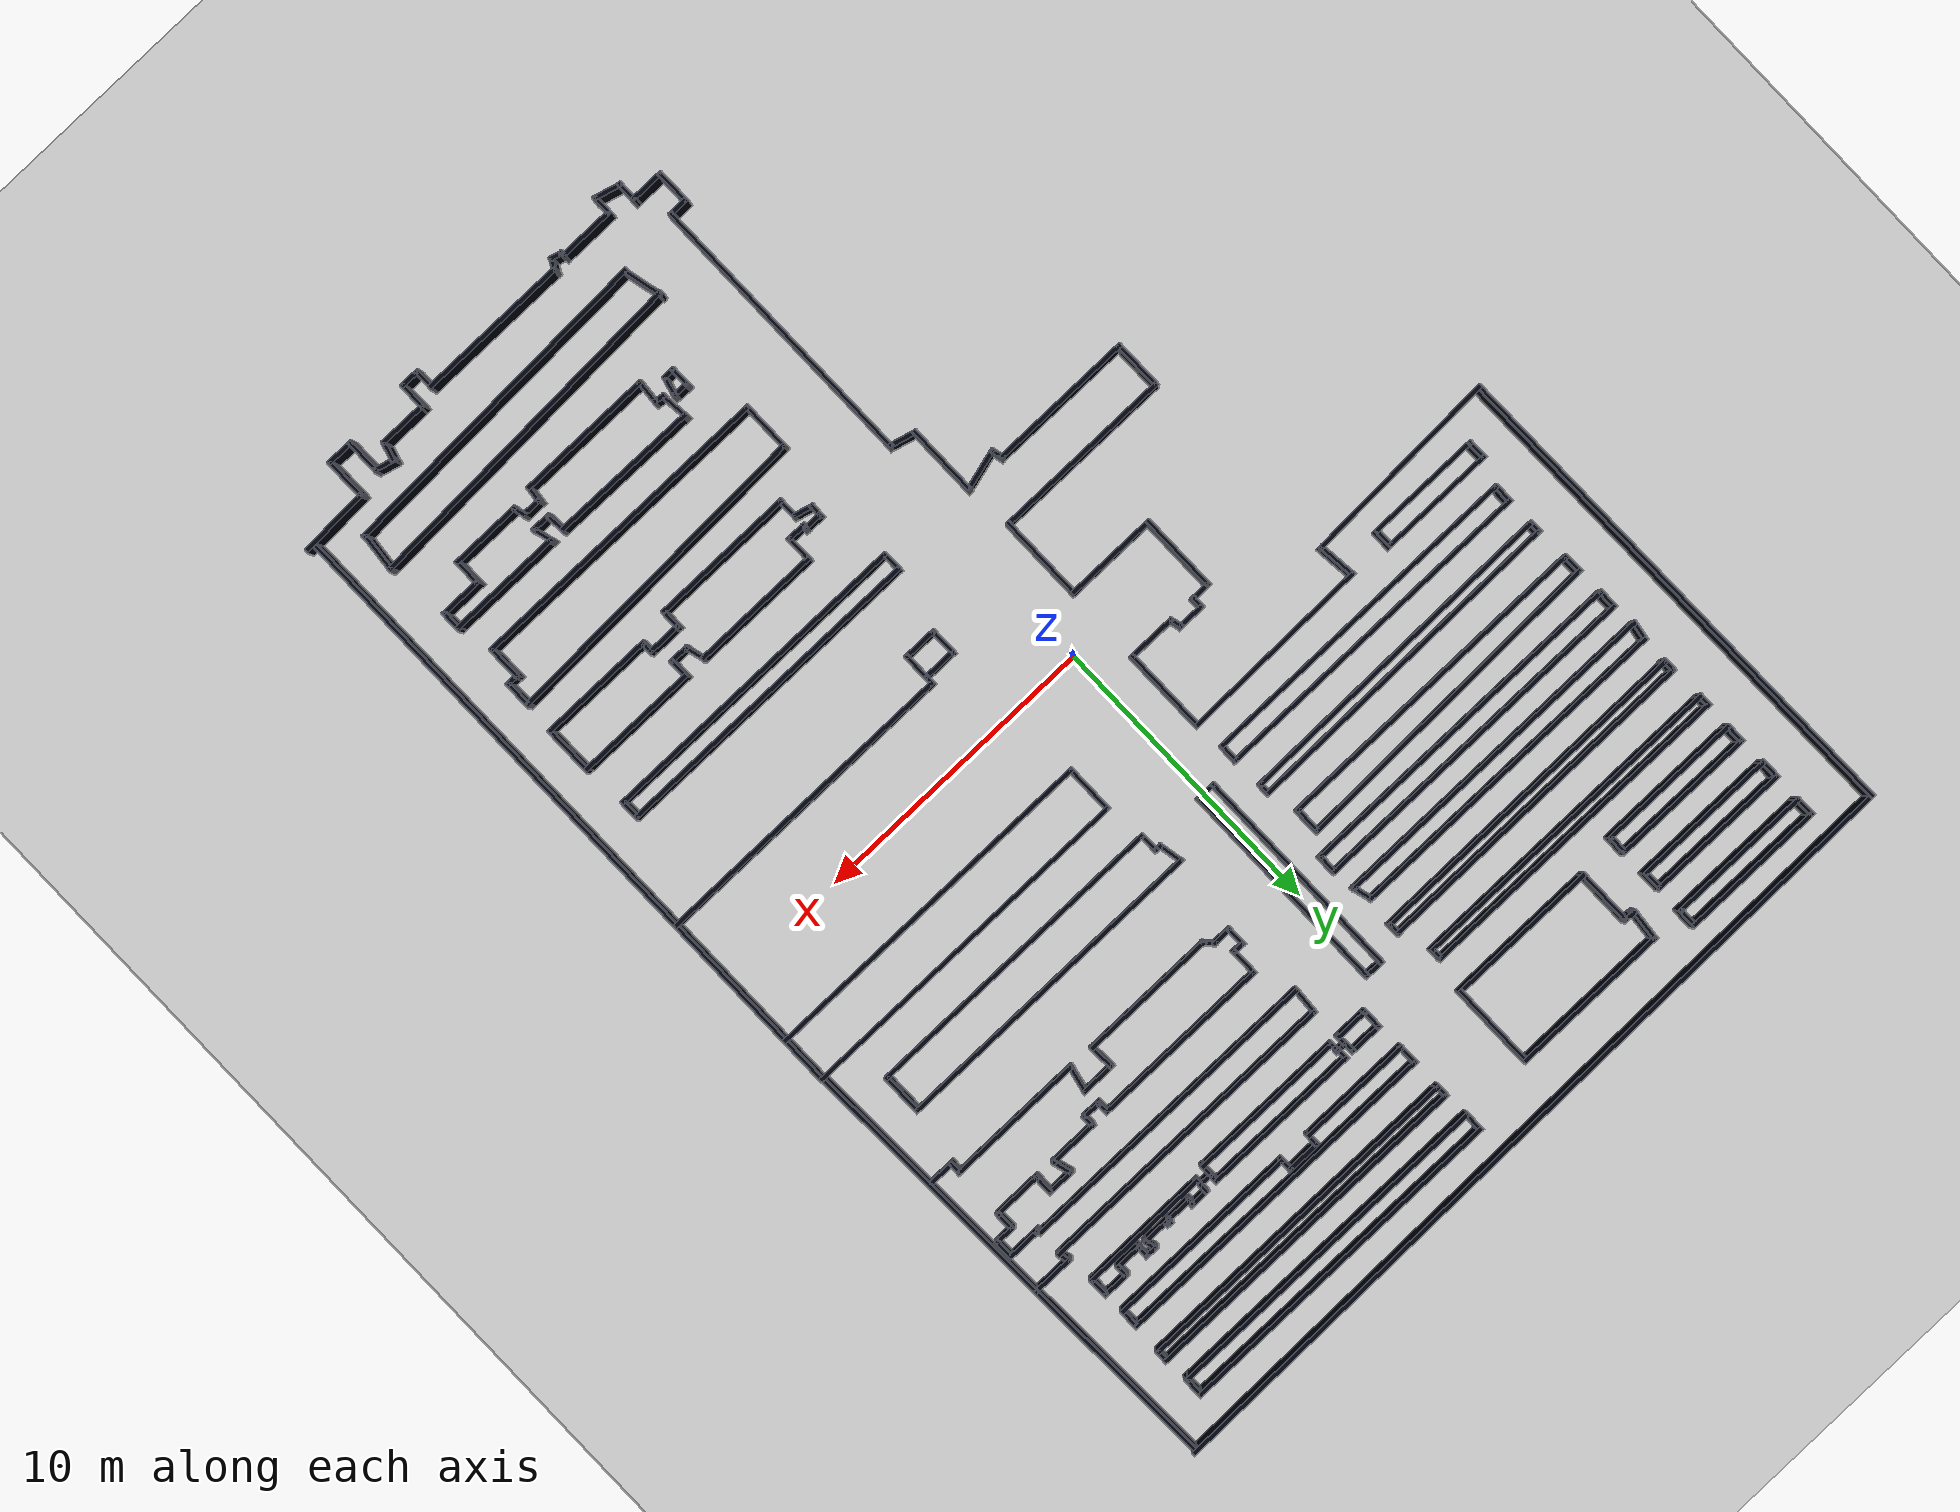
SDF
<?xml version="1.0"?>
<sdf version='1.8'>
    <world name='CDL_map'>
        <physics name='1ms' type='ignored'>
            <max_step_size>0.003</max_step_size>
            <real_time_factor>1</real_time_factor>
            <real_time_update_rate>1000</real_time_update_rate>
        </physics>
        <plugin name='ignition::gazebo::systems::Physics' filename='ignition-gazebo-physics-system' />
        <plugin name='ignition::gazebo::systems::UserCommands' filename='ignition-gazebo-user-commands-system' />
        <plugin name='ignition::gazebo::systems::SceneBroadcaster' filename='ignition-gazebo-scene-broadcaster-system' />
        <plugin name='ignition::gazebo::systems::Contact' filename='ignition-gazebo-contact-system' />
        <light name='sun' type='directional'>
            <cast_shadows>1</cast_shadows>
            <pose>0 0 10 0 -0 0</pose>
            <diffuse>0.8 0.8 0.8 1</diffuse>
            <specular>0.2 0.2 0.2 1</specular>
            <attenuation>
                <range>1000</range>
                <constant>0.90000000000000002</constant>
                <linear>0.01</linear>
                <quadratic>0.001</quadratic>
            </attenuation>
            <direction>-0.5 0.1 -0.9</direction>
            <spot>
                <inner_angle>0</inner_angle>
                <outer_angle>0</outer_angle>
                <falloff>0</falloff>
            </spot>
        </light>
        <gravity>0 0 -9.8</gravity>
        <magnetic_field>6e-06 2.3e-05 -4.2e-05</magnetic_field>
        <atmosphere type='adiabatic' />
        <scene>
            <ambient>0.4 0.4 0.4 1</ambient>
            <background>0.7 0.7 0.7 1</background>
            <shadows>1</shadows>
        </scene>
        <model name='ground_plane'>
            <static>1</static>
            <link name='link'>
                <collision name='collision'>
                    <geometry>
                        <plane>
                            <normal>0 0 1</normal>
                            <size>100 100</size>
                        </plane>
                    </geometry>
                    <surface>
                        <friction>
                            <ode />
                        </friction>
                        <bounce />
                        <contact />
                    </surface>
                </collision>
                <visual name='visual'>
                    <geometry>
                        <plane>
                            <normal>0 0 1</normal>
                            <size>100 100</size>
                        </plane>
                    </geometry>
                    <material>
                        <ambient>0.8 0.8 0.8 1</ambient>
                        <diffuse>0.8 0.8 0.8 1</diffuse>
                        <specular>0.8 0.8 0.8 1</specular>
                    </material>
                    <plugin name='__default__' filename='__default__' />
                </visual>
            </link>
            <plugin name='__default__' filename='__default__' />
            <pose>0 0 0 0 -0 0</pose>
        </model>
        <model name='border'>
            <pose>0 0 1 0 0 0</pose>
            <static>true</static>

            <link name="Wall_10">
      <pose>-4.40968 -0.081622 0 0 -0 -1.5708</pose>
    <static>true</static><collision name="Wall_10_Collision">
        <geometry>
          <box>
            <size>2.75 0.15 2.5</size>
          </box>
        </geometry>
        <pose>0 0 0 0 -0 0</pose>
      </collision>
      <visual name="Wall_10_Visual">
        <pose>0 0 0 0 -0 0</pose>
        <geometry>
          <box>
            <size>2.75 0.15 2.5</size>
          </box>
        </geometry>
        <material>
          <ambient>0.1 0.1 0.1 1</ambient>
        <diffuse>0 0.01 0.05 1</diffuse><specular>0 0.01 0.05 1</specular></material>
        </visual>
      </link>
    <link name="Wall_100">
      <pose>-12.8016 8.32753 0 0 -0 -1.5708</pose>
    <static>true</static><collision name="Wall_100_Collision">
        <geometry>
          <box>
            <size>0.75 0.15 2.5</size>
          </box>
        </geometry>
        <pose>0 0 0 0 -0 0</pose>
      </collision>
      <visual name="Wall_100_Visual">
        <pose>0 0 0 0 -0 0</pose>
        <geometry>
          <box>
            <size>0.75 0.15 2.5</size>
          </box>
        </geometry>
        <material>
          <ambient>0.1 0.1 0.1 1</ambient>
        <diffuse>0 0.01 0.05 1</diffuse><specular>0 0.01 0.05 1</specular></material>
        </visual>
      </link>
    <link name="Wall_101">
      <pose>-7.25164 8.02753 0 0 -0 0</pose>
    <static>true</static><collision name="Wall_101_Collision">
        <geometry>
          <box>
            <size>11.25 0.15 2.5</size>
          </box>
        </geometry>
        <pose>0 0 0 0 -0 0</pose>
      </collision>
      <visual name="Wall_101_Visual">
        <pose>0 0 0 0 -0 0</pose>
        <geometry>
          <box>
            <size>11.25 0.15 2.5</size>
          </box>
        </geometry>
        <material>
          <ambient>0.1 0.1 0.1 1</ambient>
        <diffuse>0 0.01 0.05 1</diffuse><specular>0 0.01 0.05 1</specular></material>
        </visual>
      </link>
    <link name="Wall_102">
      <pose>-1.70165 8.45253 0 0 -0 1.5708</pose>
    <static>true</static><collision name="Wall_102_Collision">
        <geometry>
          <box>
            <size>1 0.15 2.5</size>
          </box>
        </geometry>
        <pose>0 0 0 0 -0 0</pose>
      </collision>
      <visual name="Wall_102_Visual">
        <pose>0 0 0 0 -0 0</pose>
        <geometry>
          <box>
            <size>1 0.15 2.5</size>
          </box>
        </geometry>
        <material>
          <ambient>0.1 0.1 0.1 1</ambient>
        <diffuse>0 0.01 0.05 1</diffuse><specular>0 0.01 0.05 1</specular></material>
        </visual>
      </link>
    <link name="Wall_103">
      <pose>-7.25164 8.75253 0 0 -0 -3.11907</pose>
    <static>true</static><collision name="Wall_103_Collision">
        <geometry>
          <box>
            <size>11.2528 0.15 2.5</size>
          </box>
        </geometry>
        <pose>0 0 0 0 -0 0</pose>
      </collision>
      <visual name="Wall_103_Visual">
        <pose>0 0 0 0 -0 0</pose>
        <geometry>
          <box>
            <size>11.2528 0.15 2.5</size>
          </box>
        </geometry>
        <material>
          <ambient>0.1 0.1 0.1 1</ambient>
        <diffuse>0 0.01 0.05 1</diffuse><specular>0 0.01 0.05 1</specular></material>
        </visual>
      </link>
    <link name="Wall_105">
      <pose>-7.06163 6.98275 0 0 -0 0.010381</pose>
    <static>true</static><collision name="Wall_105_Collision">
        <geometry>
          <box>
            <size>11.4226 0.15 2.5</size>
          </box>
        </geometry>
        <pose>0 0 0 0 -0 0</pose>
      </collision>
      <visual name="Wall_105_Visual">
        <pose>0 0 0 0 -0 0</pose>
        <geometry>
          <box>
            <size>11.4226 0.15 2.5</size>
          </box>
        </geometry>
        <material>
          <ambient>0.1 0.1 0.1 1</ambient>
        <diffuse>0 0.01 0.05 1</diffuse><specular>0 0.01 0.05 1</specular></material>
        </visual>
      </link>
    <link name="Wall_106">
      <pose>-1.42564 6.86626 0 0 -0 -1.5708</pose>
    <static>true</static><collision name="Wall_106_Collision">
        <geometry>
          <box>
            <size>0.5 0.15 2.5</size>
          </box>
        </geometry>
        <pose>0 0 0 0 -0 0</pose>
      </collision>
      <visual name="Wall_106_Visual">
        <pose>0 0 0 0 -0 0</pose>
        <geometry>
          <box>
            <size>0.5 0.15 2.5</size>
          </box>
        </geometry>
        <material>
          <ambient>0.1 0.1 0.1 1</ambient>
        <diffuse>0 0.01 0.05 1</diffuse><specular>0 0.01 0.05 1</specular></material>
        </visual>
      </link>
    <link name="Wall_107">
      <pose>-7.06163 6.63275 0 0 -0 -3.13121</pose>
    <static>true</static><collision name="Wall_107_Collision">
        <geometry>
          <box>
            <size>11.4226 0.15 2.5</size>
          </box>
        </geometry>
        <pose>0 0 0 0 -0 0</pose>
      </collision>
      <visual name="Wall_107_Visual">
        <pose>0 0 0 0 -0 0</pose>
        <geometry>
          <box>
            <size>11.4226 0.15 2.5</size>
          </box>
        </geometry>
        <material>
          <ambient>0.1 0.1 0.1 1</ambient>
        <diffuse>0 0.01 0.05 1</diffuse><specular>0 0.01 0.05 1</specular></material>
        </visual>
      </link>
    <link name="Wall_108">
      <pose>-12.7366 6.74924 0 0 -0 1.5708</pose>
    <static>true</static><collision name="Wall_108_Collision">
        <geometry>
          <box>
            <size>0.5 0.15 2.5</size>
          </box>
        </geometry>
        <pose>0 0 0 0 -0 0</pose>
      </collision>
      <visual name="Wall_108_Visual">
        <pose>0 0 0 0 -0 0</pose>
        <geometry>
          <box>
            <size>0.5 0.15 2.5</size>
          </box>
        </geometry>
        <material>
          <ambient>0.1 0.1 0.1 1</ambient>
        <diffuse>0 0.01 0.05 1</diffuse><specular>0 0.01 0.05 1</specular></material>
        </visual>
      </link>
    <link name="Wall_11">
      <pose>-2.85968 -1.38162 0 0 -0 0</pose>
    <static>true</static><collision name="Wall_11_Collision">
        <geometry>
          <box>
            <size>3.25 0.15 2.5</size>
          </box>
        </geometry>
        <pose>0 0 0 0 -0 0</pose>
      </collision>
      <visual name="Wall_11_Visual">
        <pose>0 0 0 0 -0 0</pose>
        <geometry>
          <box>
            <size>3.25 0.15 2.5</size>
          </box>
        </geometry>
        <material>
          <ambient>0.1 0.1 0.1 1</ambient>
        <diffuse>0 0.01 0.05 1</diffuse><specular>0 0.01 0.05 1</specular></material>
        </visual>
      </link>
    <link name="Wall_110">
      <pose>-12.7301 5.35002 0 0 -0 -1.59246</pose>
    <static>true</static><collision name="Wall_110_Collision">
        <geometry>
          <box>
            <size>0.75 0.15 2.5</size>
          </box>
        </geometry>
        <pose>0 0 0 0 -0 0</pose>
      </collision>
      <visual name="Wall_110_Visual">
        <pose>0 0 0 0 -0 0</pose>
        <geometry>
          <box>
            <size>0.75 0.15 2.5</size>
          </box>
        </geometry>
        <material>
          <ambient>0.1 0.1 0.1 1</ambient>
        <diffuse>0 0.01 0.05 1</diffuse><specular>0 0.01 0.05 1</specular></material>
        </visual>
      </link>
    <link name="Wall_111">
      <pose>-7.06163 5.05002 0 0 -0 0</pose>
    <static>true</static><collision name="Wall_111_Collision">
        <geometry>
          <box>
            <size>11.5 0.15 2.5</size>
          </box>
        </geometry>
        <pose>0 0 0 0 -0 0</pose>
      </collision>
      <visual name="Wall_111_Visual">
        <pose>0 0 0 0 -0 0</pose>
        <geometry>
          <box>
            <size>11.5 0.15 2.5</size>
          </box>
        </geometry>
        <material>
          <ambient>0.1 0.1 0.1 1</ambient>
        <diffuse>0 0.01 0.05 1</diffuse><specular>0 0.01 0.05 1</specular></material>
        </visual>
      </link>
    <link name="Wall_112">
      <pose>-1.38013 5.35002 0 0 -0 1.54913</pose>
    <static>true</static><collision name="Wall_112_Collision">
        <geometry>
          <box>
            <size>0.75 0.15 2.5</size>
          </box>
        </geometry>
        <pose>0 0 0 0 -0 0</pose>
      </collision>
      <visual name="Wall_112_Visual">
        <pose>0 0 0 0 -0 0</pose>
        <geometry>
          <box>
            <size>0.75 0.15 2.5</size>
          </box>
        </geometry>
        <material>
          <ambient>0.1 0.1 0.1 1</ambient>
        <diffuse>0 0.01 0.05 1</diffuse><specular>0 0.01 0.05 1</specular></material>
        </visual>
      </link>
    <link name="Wall_113">
      <pose>-7.06163 5.65002 0 0 -0 3.14159</pose>
    <static>true</static><collision name="Wall_113_Collision">
        <geometry>
          <box>
            <size>11.5 0.15 2.5</size>
          </box>
        </geometry>
        <pose>0 0 0 0 -0 0</pose>
      </collision>
      <visual name="Wall_113_Visual">
        <pose>0 0 0 0 -0 0</pose>
        <geometry>
          <box>
            <size>11.5 0.15 2.5</size>
          </box>
        </geometry>
        <material>
          <ambient>0.1 0.1 0.1 1</ambient>
        <diffuse>0 0.01 0.05 1</diffuse><specular>0 0.01 0.05 1</specular></material>
        </visual>
      </link>
    <link name="Wall_115">
      <pose>-11.1416 4.1499 0 0 -0 0</pose>
    <static>true</static><collision name="Wall_115_Collision">
        <geometry>
          <box>
            <size>4 0.15 2.5</size>
          </box>
        </geometry>
        <pose>0 0 0 0 -0 0</pose>
      </collision>
      <visual name="Wall_115_Visual">
        <pose>0 0 0 0 -0 0</pose>
        <geometry>
          <box>
            <size>4 0.15 2.5</size>
          </box>
        </geometry>
        <material>
          <ambient>0.1 0.1 0.1 1</ambient>
        <diffuse>0 0.01 0.05 1</diffuse><specular>0 0.01 0.05 1</specular></material>
        </visual>
      </link>
    <link name="Wall_116">
      <pose>-9.21656 3.8499 0 0 -0 -1.5708</pose>
    <static>true</static><collision name="Wall_116_Collision">
        <geometry>
          <box>
            <size>0.75 0.15 2.5</size>
          </box>
        </geometry>
        <pose>0 0 0 0 -0 0</pose>
      </collision>
      <visual name="Wall_116_Visual">
        <pose>0 0 0 0 -0 0</pose>
        <geometry>
          <box>
            <size>0.75 0.15 2.5</size>
          </box>
        </geometry>
        <material>
          <ambient>0.1 0.1 0.1 1</ambient>
        <diffuse>0 0.01 0.05 1</diffuse><specular>0 0.01 0.05 1</specular></material>
        </visual>
      </link>
    <link name="Wall_117">
      <pose>-11.1416 3.5499 0 0 -0 3.14159</pose>
    <static>true</static><collision name="Wall_117_Collision">
        <geometry>
          <box>
            <size>4 0.15 2.5</size>
          </box>
        </geometry>
        <pose>0 0 0 0 -0 0</pose>
      </collision>
      <visual name="Wall_117_Visual">
        <pose>0 0 0 0 -0 0</pose>
        <geometry>
          <box>
            <size>4 0.15 2.5</size>
          </box>
        </geometry>
        <material>
          <ambient>0.1 0.1 0.1 1</ambient>
        <diffuse>0 0.01 0.05 1</diffuse><specular>0 0.01 0.05 1</specular></material>
        </visual>
      </link>
    <link name="Wall_118">
      <pose>-13.0666 3.8499 0 0 -0 1.5708</pose>
    <static>true</static><collision name="Wall_118_Collision">
        <geometry>
          <box>
            <size>0.75 0.15 2.5</size>
          </box>
        </geometry>
        <pose>0 0 0 0 -0 0</pose>
      </collision>
      <visual name="Wall_118_Visual">
        <pose>0 0 0 0 -0 0</pose>
        <geometry>
          <box>
            <size>0.75 0.15 2.5</size>
          </box>
        </geometry>
        <material>
          <ambient>0.1 0.1 0.1 1</ambient>
        <diffuse>0 0.01 0.05 1</diffuse><specular>0 0.01 0.05 1</specular></material>
        </visual>
      </link>
    <link name="Wall_12">
      <pose>-1.30968 -2.80662 0 0 -0 -1.5708</pose>
    <static>true</static><collision name="Wall_12_Collision">
        <geometry>
          <box>
            <size>3 0.15 2.5</size>
          </box>
        </geometry>
        <pose>0 0 0 0 -0 0</pose>
      </collision>
      <visual name="Wall_12_Visual">
        <pose>0 0 0 0 -0 0</pose>
        <geometry>
          <box>
            <size>3 0.15 2.5</size>
          </box>
        </geometry>
        <material>
          <ambient>0.1 0.1 0.1 1</ambient>
        <diffuse>0 0.01 0.05 1</diffuse><specular>0 0.01 0.05 1</specular></material>
        </visual>
      </link>
    <link name="Wall_120">
      <pose>-0.079952 13.0712 0 0 -0 0</pose>
    <static>true</static><collision name="Wall_120_Collision">
        <geometry>
          <box>
            <size>0.75 0.15 2.5</size>
          </box>
        </geometry>
        <pose>0 0 0 0 -0 0</pose>
      </collision>
      <visual name="Wall_120_Visual">
        <pose>0 0 0 0 -0 0</pose>
        <geometry>
          <box>
            <size>0.75 0.15 2.5</size>
          </box>
        </geometry>
        <material>
          <ambient>0.1 0.1 0.1 1</ambient>
        <diffuse>0 0.01 0.05 1</diffuse><specular>0 0.01 0.05 1</specular></material>
        </visual>
      </link>
    <link name="Wall_121">
      <pose>0.220048 9.39615 0 0 -0 -1.5708</pose>
    <static>true</static><collision name="Wall_121_Collision">
        <geometry>
          <box>
            <size>7.5 0.15 2.5</size>
          </box>
        </geometry>
        <pose>0 0 0 0 -0 0</pose>
      </collision>
      <visual name="Wall_121_Visual">
        <pose>0 0 0 0 -0 0</pose>
        <geometry>
          <box>
            <size>7.5 0.15 2.5</size>
          </box>
        </geometry>
        <material>
          <ambient>0.1 0.1 0.1 1</ambient>
        <diffuse>0 0.01 0.05 1</diffuse><specular>0 0.01 0.05 1</specular></material>
        </visual>
      </link>
    <link name="Wall_122">
      <pose>-0.079952 5.72115 0 0 -0 3.14159</pose>
    <static>true</static><collision name="Wall_122_Collision">
        <geometry>
          <box>
            <size>0.75 0.15 2.5</size>
          </box>
        </geometry>
        <pose>0 0 0 0 -0 0</pose>
      </collision>
      <visual name="Wall_122_Visual">
        <pose>0 0 0 0 -0 0</pose>
        <geometry>
          <box>
            <size>0.75 0.15 2.5</size>
          </box>
        </geometry>
        <material>
          <ambient>0.1 0.1 0.1 1</ambient>
        <diffuse>0 0.01 0.05 1</diffuse><specular>0 0.01 0.05 1</specular></material>
        </visual>
      </link>
    <link name="Wall_123">
      <pose>-0.379952 9.39615 0 0 -0 1.5708</pose>
    <static>true</static><collision name="Wall_123_Collision">
        <geometry>
          <box>
            <size>7.5 0.15 2.5</size>
          </box>
        </geometry>
        <pose>0 0 0 0 -0 0</pose>
      </collision>
      <visual name="Wall_123_Visual">
        <pose>0 0 0 0 -0 0</pose>
        <geometry>
          <box>
            <size>7.5 0.15 2.5</size>
          </box>
        </geometry>
        <material>
          <ambient>0.1 0.1 0.1 1</ambient>
        <diffuse>0 0.01 0.05 1</diffuse><specular>0 0.01 0.05 1</specular></material>
        </visual>
      </link>
    <link name="Wall_125">
      <pose>6.72296 18.1772 0 0 -0 0</pose>
    <static>true</static><collision name="Wall_125_Collision">
        <geometry>
          <box>
            <size>11.75 0.15 2.5</size>
          </box>
        </geometry>
        <pose>0 0 0 0 -0 0</pose>
      </collision>
      <visual name="Wall_125_Visual">
        <pose>0 0 0 0 -0 0</pose>
        <geometry>
          <box>
            <size>11.75 0.15 2.5</size>
          </box>
        </geometry>
        <material>
          <ambient>0.1 0.1 0.1 1</ambient>
        <diffuse>0 0.01 0.05 1</diffuse><specular>0 0.01 0.05 1</specular></material>
        </visual>
      </link>
    <link name="Wall_126">
      <pose>12.523 18.4772 0 0 -0 1.5708</pose>
    <static>true</static><collision name="Wall_126_Collision">
        <geometry>
          <box>
            <size>0.75 0.15 2.5</size>
          </box>
        </geometry>
        <pose>0 0 0 0 -0 0</pose>
      </collision>
      <visual name="Wall_126_Visual">
        <pose>0 0 0 0 -0 0</pose>
        <geometry>
          <box>
            <size>0.75 0.15 2.5</size>
          </box>
        </geometry>
        <material>
          <ambient>0.1 0.1 0.1 1</ambient>
        <diffuse>0 0.01 0.05 1</diffuse><specular>0 0.01 0.05 1</specular></material>
        </visual>
      </link>
    <link name="Wall_127">
      <pose>6.72296 18.7772 0 0 -0 3.14159</pose>
    <static>true</static><collision name="Wall_127_Collision">
        <geometry>
          <box>
            <size>11.75 0.15 2.5</size>
          </box>
        </geometry>
        <pose>0 0 0 0 -0 0</pose>
      </collision>
      <visual name="Wall_127_Visual">
        <pose>0 0 0 0 -0 0</pose>
        <geometry>
          <box>
            <size>11.75 0.15 2.5</size>
          </box>
        </geometry>
        <material>
          <ambient>0.1 0.1 0.1 1</ambient>
        <diffuse>0 0.01 0.05 1</diffuse><specular>0 0.01 0.05 1</specular></material>
        </visual>
      </link>
    <link name="Wall_128">
      <pose>0.922962 18.4772 0 0 -0 -1.5708</pose>
    <static>true</static><collision name="Wall_128_Collision">
        <geometry>
          <box>
            <size>0.75 0.15 2.5</size>
          </box>
        </geometry>
        <pose>0 0 0 0 -0 0</pose>
      </collision>
      <visual name="Wall_128_Visual">
        <pose>0 0 0 0 -0 0</pose>
        <geometry>
          <box>
            <size>0.75 0.15 2.5</size>
          </box>
        </geometry>
        <material>
          <ambient>0.1 0.1 0.1 1</ambient>
        <diffuse>0 0.01 0.05 1</diffuse><specular>0 0.01 0.05 1</specular></material>
        </visual>
      </link>
    <link name="Wall_13">
      <pose>-4.35968 -4.23162 0 0 -0 3.14159</pose>
    <static>true</static><collision name="Wall_13_Collision">
        <geometry>
          <box>
            <size>6.25 0.15 2.5</size>
          </box>
        </geometry>
        <pose>0 0 0 0 -0 0</pose>
      </collision>
      <visual name="Wall_13_Visual">
        <pose>0 0 0 0 -0 0</pose>
        <geometry>
          <box>
            <size>6.25 0.15 2.5</size>
          </box>
        </geometry>
        <material>
          <ambient>0.1 0.1 0.1 1</ambient>
        <diffuse>0 0.01 0.05 1</diffuse><specular>0 0.01 0.05 1</specular></material>
        </visual>
      </link>
    <link name="Wall_130">
      <pose>6.77468 17.3239 0 0 -0 0</pose>
    <static>true</static><collision name="Wall_130_Collision">
        <geometry>
          <box>
            <size>11.75 0.15 2.5</size>
          </box>
        </geometry>
        <pose>0 0 0 0 -0 0</pose>
      </collision>
      <visual name="Wall_130_Visual">
        <pose>0 0 0 0 -0 0</pose>
        <geometry>
          <box>
            <size>11.75 0.15 2.5</size>
          </box>
        </geometry>
        <material>
          <ambient>0.1 0.1 0.1 1</ambient>
        <diffuse>0 0.01 0.05 1</diffuse><specular>0 0.01 0.05 1</specular></material>
        </visual>
      </link>
    <link name="Wall_131">
      <pose>12.5747 17.1489 0 0 -0 -1.5708</pose>
    <static>true</static><collision name="Wall_131_Collision">
        <geometry>
          <box>
            <size>0.5 0.15 2.5</size>
          </box>
        </geometry>
        <pose>0 0 0 0 -0 0</pose>
      </collision>
      <visual name="Wall_131_Visual">
        <pose>0 0 0 0 -0 0</pose>
        <geometry>
          <box>
            <size>0.5 0.15 2.5</size>
          </box>
        </geometry>
        <material>
          <ambient>0.1 0.1 0.1 1</ambient>
        <diffuse>0 0.01 0.05 1</diffuse><specular>0 0.01 0.05 1</specular></material>
        </visual>
      </link>
    <link name="Wall_132">
      <pose>6.77468 16.9739 0 0 -0 3.14159</pose>
    <static>true</static><collision name="Wall_132_Collision">
        <geometry>
          <box>
            <size>11.75 0.15 2.5</size>
          </box>
        </geometry>
        <pose>0 0 0 0 -0 0</pose>
      </collision>
      <visual name="Wall_132_Visual">
        <pose>0 0 0 0 -0 0</pose>
        <geometry>
          <box>
            <size>11.75 0.15 2.5</size>
          </box>
        </geometry>
        <material>
          <ambient>0.1 0.1 0.1 1</ambient>
        <diffuse>0 0.01 0.05 1</diffuse><specular>0 0.01 0.05 1</specular></material>
        </visual>
      </link>
    <link name="Wall_133">
      <pose>0.974678 17.1489 0 0 -0 1.5708</pose>
    <static>true</static><collision name="Wall_133_Collision">
        <geometry>
          <box>
            <size>0.5 0.15 2.5</size>
          </box>
        </geometry>
        <pose>0 0 0 0 -0 0</pose>
      </collision>
      <visual name="Wall_133_Visual">
        <pose>0 0 0 0 -0 0</pose>
        <geometry>
          <box>
            <size>0.5 0.15 2.5</size>
          </box>
        </geometry>
        <material>
          <ambient>0.1 0.1 0.1 1</ambient>
        <diffuse>0 0.01 0.05 1</diffuse><specular>0 0.01 0.05 1</specular></material>
        </visual>
      </link>
    <link name="Wall_135">
      <pose>0.961749 15.6534 0 0 -0 -1.5708</pose>
    <static>true</static><collision name="Wall_135_Collision">
        <geometry>
          <box>
            <size>0.75 0.15 2.5</size>
          </box>
        </geometry>
        <pose>0 0 0 0 -0 0</pose>
      </collision>
      <visual name="Wall_135_Visual">
        <pose>0 0 0 0 -0 0</pose>
        <geometry>
          <box>
            <size>0.75 0.15 2.5</size>
          </box>
        </geometry>
        <material>
          <ambient>0.1 0.1 0.1 1</ambient>
        <diffuse>0 0.01 0.05 1</diffuse><specular>0 0.01 0.05 1</specular></material>
        </visual>
      </link>
    <link name="Wall_136">
      <pose>2.88675 15.3534 0 0 -0 0</pose>
    <static>true</static><collision name="Wall_136_Collision">
        <geometry>
          <box>
            <size>4 0.15 2.5</size>
          </box>
        </geometry>
        <pose>0 0 0 0 -0 0</pose>
      </collision>
      <visual name="Wall_136_Visual">
        <pose>0 0 0 0 -0 0</pose>
        <geometry>
          <box>
            <size>4 0.15 2.5</size>
          </box>
        </geometry>
        <material>
          <ambient>0.1 0.1 0.1 1</ambient>
        <diffuse>0 0.01 0.05 1</diffuse><specular>0 0.01 0.05 1</specular></material>
        </visual>
      </link>
    <link name="Wall_137">
      <pose>4.81175 15.5284 0 0 -0 1.5708</pose>
    <static>true</static><collision name="Wall_137_Collision">
        <geometry>
          <box>
            <size>0.5 0.15 2.5</size>
          </box>
        </geometry>
        <pose>0 0 0 0 -0 0</pose>
      </collision>
      <visual name="Wall_137_Visual">
        <pose>0 0 0 0 -0 0</pose>
        <geometry>
          <box>
            <size>0.5 0.15 2.5</size>
          </box>
        </geometry>
        <material>
          <ambient>0.1 0.1 0.1 1</ambient>
        <diffuse>0 0.01 0.05 1</diffuse><specular>0 0.01 0.05 1</specular></material>
        </visual>
      </link>
    <link name="Wall_138">
      <pose>5.36175 15.7034 0 0 -0 0</pose>
    <static>true</static><collision name="Wall_138_Collision">
        <geometry>
          <box>
            <size>1.25 0.15 2.5</size>
          </box>
        </geometry>
        <pose>0 0 0 0 -0 0</pose>
      </collision>
      <visual name="Wall_138_Visual">
        <pose>0 0 0 0 -0 0</pose>
        <geometry>
          <box>
            <size>1.25 0.15 2.5</size>
          </box>
        </geometry>
        <material>
          <ambient>0.1 0.1 0.1 1</ambient>
        <diffuse>0 0.01 0.05 1</diffuse><specular>0 0.01 0.05 1</specular></material>
        </visual>
      </link>
    <link name="Wall_139">
      <pose>5.91175 15.5284 0 0 -0 -1.5708</pose>
    <static>true</static><collision name="Wall_139_Collision">
        <geometry>
          <box>
            <size>0.5 0.15 2.5</size>
          </box>
        </geometry>
        <pose>0 0 0 0 -0 0</pose>
      </collision>
      <visual name="Wall_139_Visual">
        <pose>0 0 0 0 -0 0</pose>
        <geometry>
          <box>
            <size>0.5 0.15 2.5</size>
          </box>
        </geometry>
        <material>
          <ambient>0.1 0.1 0.1 1</ambient>
        <diffuse>0 0.01 0.05 1</diffuse><specular>0 0.01 0.05 1</specular></material>
        </visual>
      </link>
    <link name="Wall_14">
      <pose>-7.40968 -5.03162 0 0 -0 -1.5708</pose>
    <static>true</static><collision name="Wall_14_Collision">
        <geometry>
          <box>
            <size>1.75 0.15 2.5</size>
          </box>
        </geometry>
        <pose>0 0 0 0 -0 0</pose>
      </collision>
      <visual name="Wall_14_Visual">
        <pose>0 0 0 0 -0 0</pose>
        <geometry>
          <box>
            <size>1.75 0.15 2.5</size>
          </box>
        </geometry>
        <material>
          <ambient>0.1 0.1 0.1 1</ambient>
        <diffuse>0 0.01 0.05 1</diffuse><specular>0 0.01 0.05 1</specular></material>
        </visual>
      </link>
    <link name="Wall_140">
      <pose>9.21175 15.3534 0 0 -0 0</pose>
    <static>true</static><collision name="Wall_140_Collision">
        <geometry>
          <box>
            <size>6.75 0.15 2.5</size>
          </box>
        </geometry>
        <pose>0 0 0 0 -0 0</pose>
      </collision>
      <visual name="Wall_140_Visual">
        <pose>0 0 0 0 -0 0</pose>
        <geometry>
          <box>
            <size>6.75 0.15 2.5</size>
          </box>
        </geometry>
        <material>
          <ambient>0.1 0.1 0.1 1</ambient>
        <diffuse>0 0.01 0.05 1</diffuse><specular>0 0.01 0.05 1</specular></material>
        </visual>
      </link>
    <link name="Wall_141">
      <pose>12.5117 15.6534 0 0 -0 1.5708</pose>
    <static>true</static><collision name="Wall_141_Collision">
        <geometry>
          <box>
            <size>0.75 0.15 2.5</size>
          </box>
        </geometry>
        <pose>0 0 0 0 -0 0</pose>
      </collision>
      <visual name="Wall_141_Visual">
        <pose>0 0 0 0 -0 0</pose>
        <geometry>
          <box>
            <size>0.75 0.15 2.5</size>
          </box>
        </geometry>
        <material>
          <ambient>0.1 0.1 0.1 1</ambient>
        <diffuse>0 0.01 0.05 1</diffuse><specular>0 0.01 0.05 1</specular></material>
        </visual>
      </link>
    <link name="Wall_142">
      <pose>6.73675 15.9534 0 0 -0 3.14159</pose>
    <static>true</static><collision name="Wall_142_Collision">
        <geometry>
          <box>
            <size>11.7 0.15 2.5</size>
          </box>
        </geometry>
        <pose>0 0 0 0 -0 0</pose>
      </collision>
      <visual name="Wall_142_Visual">
        <pose>0 0 0 0 -0 0</pose>
        <geometry>
          <box>
            <size>11.7 0.15 2.5</size>
          </box>
        </geometry>
        <material>
          <ambient>0.1 0.1 0.1 1</ambient>
        <diffuse>0 0.01 0.05 1</diffuse><specular>0 0.01 0.05 1</specular></material>
        </visual>
      </link>
    <link name="Wall_144">
      <pose>1.01346 14.1278 0 0 -0 -1.5708</pose>
    <static>true</static><collision name="Wall_144_Collision">
        <geometry>
          <box>
            <size>0.75 0.15 2.5</size>
          </box>
        </geometry>
        <pose>0 0 0 0 -0 0</pose>
      </collision>
      <visual name="Wall_144_Visual">
        <pose>0 0 0 0 -0 0</pose>
        <geometry>
          <box>
            <size>0.75 0.15 2.5</size>
          </box>
        </geometry>
        <material>
          <ambient>0.1 0.1 0.1 1</ambient>
        <diffuse>0 0.01 0.05 1</diffuse><specular>0 0.01 0.05 1</specular></material>
        </visual>
      </link>
    <link name="Wall_145">
      <pose>1.56346 13.8278 0 0 -0 0</pose>
    <static>true</static><collision name="Wall_145_Collision">
        <geometry>
          <box>
            <size>1.25 0.15 2.5</size>
          </box>
        </geometry>
        <pose>0 0 0 0 -0 0</pose>
      </collision>
      <visual name="Wall_145_Visual">
        <pose>0 0 0 0 -0 0</pose>
        <geometry>
          <box>
            <size>1.25 0.15 2.5</size>
          </box>
        </geometry>
        <material>
          <ambient>0.1 0.1 0.1 1</ambient>
        <diffuse>0 0.01 0.05 1</diffuse><specular>0 0.01 0.05 1</specular></material>
        </visual>
      </link>
    <link name="Wall_146">
      <pose>2.10152 14.1251 0 0 -0 1.61096</pose>
    <static>true</static><collision name="Wall_146_Collision">
        <geometry>
          <box>
            <size>0.744967 0.15 2.5</size>
          </box>
        </geometry>
        <pose>0 0 0 0 -0 0</pose>
      </collision>
      <visual name="Wall_146_Visual">
        <pose>0 0 0 0 -0 0</pose>
        <geometry>
          <box>
            <size>0.744967 0.15 2.5</size>
          </box>
        </geometry>
        <material>
          <ambient>0.1 0.1 0.1 1</ambient>
        <diffuse>0 0.01 0.05 1</diffuse><specular>0 0.01 0.05 1</specular></material>
        </visual>
      </link>
    <link name="Wall_147">
      <pose>1.55152 14.4251 0 0 -0 3.13647</pose>
    <static>true</static><collision name="Wall_147_Collision">
        <geometry>
          <box>
            <size>1.22617 0.15 2.5</size>
          </box>
        </geometry>
        <pose>0 0 0 0 -0 0</pose>
      </collision>
      <visual name="Wall_147_Visual">
        <pose>0 0 0 0 -0 0</pose>
        <geometry>
          <box>
            <size>1.22617 0.15 2.5</size>
          </box>
        </geometry>
        <material>
          <ambient>0.1 0.1 0.1 1</ambient>
        <diffuse>0 0.01 0.05 1</diffuse><specular>0 0.01 0.05 1</specular></material>
        </visual>
      </link>
    <link name="Wall_149">
      <pose>2.39783 14.138 0 0 -0 -1.53063</pose>
    <static>true</static><collision name="Wall_149_Collision">
        <geometry>
          <box>
            <size>0.744967 0.15 2.5</size>
          </box>
        </geometry>
        <pose>0 0 0 0 -0 0</pose>
      </collision>
      <visual name="Wall_149_Visual">
        <pose>0 0 0 0 -0 0</pose>
        <geometry>
          <box>
            <size>0.744967 0.15 2.5</size>
          </box>
        </geometry>
        <material>
          <ambient>0.1 0.1 0.1 1</ambient>
        <diffuse>0 0.01 0.05 1</diffuse><specular>0 0.01 0.05 1</specular></material>
        </visual>
      </link>
    <link name="Wall_15">
      <pose>-4.98468 -5.83162 0 0 -0 0</pose>
    <static>true</static><collision name="Wall_15_Collision">
        <geometry>
          <box>
            <size>5 0.15 2.5</size>
          </box>
        </geometry>
        <pose>0 0 0 0 -0 0</pose>
      </collision>
      <visual name="Wall_15_Visual">
        <pose>0 0 0 0 -0 0</pose>
        <geometry>
          <box>
            <size>5 0.15 2.5</size>
          </box>
        </geometry>
        <material>
          <ambient>0.1 0.1 0.1 1</ambient>
        <diffuse>0 0.01 0.05 1</diffuse><specular>0 0.01 0.05 1</specular></material>
        </visual>
      </link>
    <link name="Wall_150">
      <pose>5.08478 13.8408 0 0 -0 0</pose>
    <static>true</static><collision name="Wall_150_Collision">
        <geometry>
          <box>
            <size>5.5 0.15 2.5</size>
          </box>
        </geometry>
        <pose>0 0 0 0 -0 0</pose>
      </collision>
      <visual name="Wall_150_Visual">
        <pose>0 0 0 0 -0 0</pose>
        <geometry>
          <box>
            <size>5.5 0.15 2.5</size>
          </box>
        </geometry>
        <material>
          <ambient>0.1 0.1 0.1 1</ambient>
        <diffuse>0 0.01 0.05 1</diffuse><specular>0 0.01 0.05 1</specular></material>
        </visual>
      </link>
    <link name="Wall_151">
      <pose>7.75978 14.1408 0 0 -0 1.5708</pose>
    <static>true</static><collision name="Wall_151_Collision">
        <geometry>
          <box>
            <size>0.75 0.15 2.5</size>
          </box>
        </geometry>
        <pose>0 0 0 0 -0 0</pose>
      </collision>
      <visual name="Wall_151_Visual">
        <pose>0 0 0 0 -0 0</pose>
        <geometry>
          <box>
            <size>0.75 0.15 2.5</size>
          </box>
        </geometry>
        <material>
          <ambient>0.1 0.1 0.1 1</ambient>
        <diffuse>0 0.01 0.05 1</diffuse><specular>0 0.01 0.05 1</specular></material>
        </visual>
      </link>
    <link name="Wall_152">
      <pose>5.07283 14.438 0 0 -0 -3.14057</pose>
    <static>true</static><collision name="Wall_152_Collision">
        <geometry>
          <box>
            <size>5.5239 0.15 2.5</size>
          </box>
        </geometry>
        <pose>0 0 0 0 -0 0</pose>
      </collision>
      <visual name="Wall_152_Visual">
        <pose>0 0 0 0 -0 0</pose>
        <geometry>
          <box>
            <size>5.5239 0.15 2.5</size>
          </box>
        </geometry>
        <material>
          <ambient>0.1 0.1 0.1 1</ambient>
        <diffuse>0 0.01 0.05 1</diffuse><specular>0 0.01 0.05 1</specular></material>
        </visual>
      </link>
    <link name="Wall_157">
      <pose>2.26628 14.1135 0 0 -0 0</pose>
    <static>true</static><collision name="Wall_157_Collision">
        <geometry>
          <box>
            <size>0.5 0.15 2.5</size>
          </box>
        </geometry>
        <pose>0 0 0 0 -0 0</pose>
      </collision>
      <visual name="Wall_157_Visual">
        <pose>0 0 0 0 -0 0</pose>
        <geometry>
          <box>
            <size>0.5 0.15 2.5</size>
          </box>
        </geometry>
        <material>
          <ambient>0.1 0.1 0.1 1</ambient>
        <diffuse>0 0.01 0.05 1</diffuse><specular>0 0.01 0.05 1</specular></material>
        </visual>
      </link>
    <link name="Wall_159">
      <pose>8.19109 14.241 0 0 -0 -1.59747</pose>
    <static>true</static><collision name="Wall_159_Collision">
        <geometry>
          <box>
            <size>0.566927 0.15 2.5</size>
          </box>
        </geometry>
        <pose>0 0 0 0 -0 0</pose>
      </collision>
      <visual name="Wall_159_Visual">
        <pose>0 0 0 0 -0 0</pose>
        <geometry>
          <box>
            <size>0.566927 0.15 2.5</size>
          </box>
        </geometry>
        <material>
          <ambient>0.1 0.1 0.1 1</ambient>
        <diffuse>0 0.01 0.05 1</diffuse><specular>0 0.01 0.05 1</specular></material>
        </visual>
      </link>
    <link name="Wall_16">
      <pose>-2.51438 -6.00066 0 0 -0 -1.309</pose>
    <static>true</static><collision name="Wall_16_Collision">
        <geometry>
          <box>
            <size>0.5 0.15 2.5</size>
          </box>
        </geometry>
        <pose>0 0 0 0 -0 0</pose>
      </collision>
      <visual name="Wall_16_Visual">
        <pose>0 0 0 0 -0 0</pose>
        <geometry>
          <box>
            <size>0.5 0.15 2.5</size>
          </box>
        </geometry>
        <material>
          <ambient>0.1 0.1 0.1 1</ambient>
        <diffuse>0 0.01 0.05 1</diffuse><specular>0 0.01 0.05 1</specular></material>
        </visual>
      </link>
    <link name="Wall_161">
      <pose>10.3605 14.0326 0 0 -0 0</pose>
    <static>true</static><collision name="Wall_161_Collision">
        <geometry>
          <box>
            <size>4.5 0.15 2.5</size>
          </box>
        </geometry>
        <pose>0 0 0 0 -0 0</pose>
      </collision>
      <visual name="Wall_161_Visual">
        <pose>0 0 0 0 -0 0</pose>
        <geometry>
          <box>
            <size>4.5 0.15 2.5</size>
          </box>
        </geometry>
        <material>
          <ambient>0.1 0.1 0.1 1</ambient>
        <diffuse>0 0.01 0.05 1</diffuse><specular>0 0.01 0.05 1</specular></material>
        </visual>
      </link>
    <link name="Wall_162">
      <pose>12.5355 14.3326 0 0 -0 1.5708</pose>
    <static>true</static><collision name="Wall_162_Collision">
        <geometry>
          <box>
            <size>0.75 0.15 2.5</size>
          </box>
        </geometry>
        <pose>0 0 0 0 -0 0</pose>
      </collision>
      <visual name="Wall_162_Visual">
        <pose>0 0 0 0 -0 0</pose>
        <geometry>
          <box>
            <size>0.75 0.15 2.5</size>
          </box>
        </geometry>
        <material>
          <ambient>0.1 0.1 0.1 1</ambient>
        <diffuse>0 0.01 0.05 1</diffuse><specular>0 0.01 0.05 1</specular></material>
        </visual>
      </link>
    <link name="Wall_163">
      <pose>12.1105 14.6326 0 0 -0 3.14159</pose>
    <static>true</static><collision name="Wall_163_Collision">
        <geometry>
          <box>
            <size>1 0.15 2.5</size>
          </box>
        </geometry>
        <pose>0 0 0 0 -0 0</pose>
      </collision>
      <visual name="Wall_163_Visual">
        <pose>0 0 0 0 -0 0</pose>
        <geometry>
          <box>
            <size>1 0.15 2.5</size>
          </box>
        </geometry>
        <material>
          <ambient>0.1 0.1 0.1 1</ambient>
        <diffuse>0 0.01 0.05 1</diffuse><specular>0 0.01 0.05 1</specular></material>
        </visual>
      </link>
    <link name="Wall_164">
      <pose>11.6855 14.4576 0 0 -0 -1.5708</pose>
    <static>true</static><collision name="Wall_164_Collision">
        <geometry>
          <box>
            <size>0.5 0.15 2.5</size>
          </box>
        </geometry>
        <pose>0 0 0 0 -0 0</pose>
      </collision>
      <visual name="Wall_164_Visual">
        <pose>0 0 0 0 -0 0</pose>
        <geometry>
          <box>
            <size>0.5 0.15 2.5</size>
          </box>
        </geometry>
        <material>
          <ambient>0.1 0.1 0.1 1</ambient>
        <diffuse>0 0.01 0.05 1</diffuse><specular>0 0.01 0.05 1</specular></material>
        </visual>
      </link>
    <link name="Wall_165">
      <pose>11.2605 14.2826 0 0 -0 3.14159</pose>
    <static>true</static><collision name="Wall_165_Collision">
        <geometry>
          <box>
            <size>1 0.15 2.5</size>
          </box>
        </geometry>
        <pose>0 0 0 0 -0 0</pose>
      </collision>
      <visual name="Wall_165_Visual">
        <pose>0 0 0 0 -0 0</pose>
        <geometry>
          <box>
            <size>1 0.15 2.5</size>
          </box>
        </geometry>
        <material>
          <ambient>0.1 0.1 0.1 1</ambient>
        <diffuse>0 0.01 0.05 1</diffuse><specular>0 0.01 0.05 1</specular></material>
        </visual>
      </link>
    <link name="Wall_166">
      <pose>10.8355 14.4576 0 0 -0 1.5708</pose>
    <static>true</static><collision name="Wall_166_Collision">
        <geometry>
          <box>
            <size>0.5 0.15 2.5</size>
          </box>
        </geometry>
        <pose>0 0 0 0 -0 0</pose>
      </collision>
      <visual name="Wall_166_Visual">
        <pose>0 0 0 0 -0 0</pose>
        <geometry>
          <box>
            <size>0.5 0.15 2.5</size>
          </box>
        </geometry>
        <material>
          <ambient>0.1 0.1 0.1 1</ambient>
        <diffuse>0 0.01 0.05 1</diffuse><specular>0 0.01 0.05 1</specular></material>
        </visual>
      </link>
    <link name="Wall_167">
      <pose>10.6605 14.6326 0 0 -0 3.14159</pose>
    <static>true</static><collision name="Wall_167_Collision">
        <geometry>
          <box>
            <size>0.5 0.15 2.5</size>
          </box>
        </geometry>
        <pose>0 0 0 0 -0 0</pose>
      </collision>
      <visual name="Wall_167_Visual">
        <pose>0 0 0 0 -0 0</pose>
        <geometry>
          <box>
            <size>0.5 0.15 2.5</size>
          </box>
        </geometry>
        <material>
          <ambient>0.1 0.1 0.1 1</ambient>
        <diffuse>0 0.01 0.05 1</diffuse><specular>0 0.01 0.05 1</specular></material>
        </visual>
      </link>
    <link name="Wall_168">
      <pose>10.5308 14.4636 0 0 -0 -1.309</pose>
    <static>true</static><collision name="Wall_168_Collision">
        <geometry>
          <box>
            <size>0.5 0.15 2.5</size>
          </box>
        </geometry>
        <pose>0 0 0 0 -0 0</pose>
      </collision>
      <visual name="Wall_168_Visual">
        <pose>0 0 0 0 -0 0</pose>
        <geometry>
          <box>
            <size>0.5 0.15 2.5</size>
          </box>
        </geometry>
        <material>
          <ambient>0.1 0.1 0.1 1</ambient>
        <diffuse>0 0.01 0.05 1</diffuse><specular>0 0.01 0.05 1</specular></material>
        </visual>
      </link>
    <link name="Wall_169">
      <pose>10.1511 14.2945 0 0 -0 3.14159</pose>
    <static>true</static><collision name="Wall_169_Collision">
        <geometry>
          <box>
            <size>1 0.15 2.5</size>
          </box>
        </geometry>
        <pose>0 0 0 0 -0 0</pose>
      </collision>
      <visual name="Wall_169_Visual">
        <pose>0 0 0 0 -0 0</pose>
        <geometry>
          <box>
            <size>1 0.15 2.5</size>
          </box>
        </geometry>
        <material>
          <ambient>0.1 0.1 0.1 1</ambient>
        <diffuse>0 0.01 0.05 1</diffuse><specular>0 0.01 0.05 1</specular></material>
        </visual>
      </link>
    <link name="Wall_17">
      <pose>-1.81709 -5.99499 0 0 -0 0.261799</pose>
    <static>true</static><collision name="Wall_17_Collision">
        <geometry>
          <box>
            <size>1.5 0.15 2.5</size>
          </box>
        </geometry>
        <pose>0 0 0 0 -0 0</pose>
      </collision>
      <visual name="Wall_17_Visual">
        <pose>0 0 0 0 -0 0</pose>
        <geometry>
          <box>
            <size>1.5 0.15 2.5</size>
          </box>
        </geometry>
        <material>
          <ambient>0.1 0.1 0.1 1</ambient>
        <diffuse>0 0.01 0.05 1</diffuse><specular>0 0.01 0.05 1</specular></material>
        </visual>
      </link>
    <link name="Wall_170">
      <pose>9.72612 14.3445 0 0 -0 1.5708</pose>
    <static>true</static><collision name="Wall_170_Collision">
        <geometry>
          <box>
            <size>0.25 0.15 2.5</size>
          </box>
        </geometry>
        <pose>0 0 0 0 -0 0</pose>
      </collision>
      <visual name="Wall_170_Visual">
        <pose>0 0 0 0 -0 0</pose>
        <geometry>
          <box>
            <size>0.25 0.15 2.5</size>
          </box>
        </geometry>
        <material>
          <ambient>0.1 0.1 0.1 1</ambient>
        <diffuse>0 0.01 0.05 1</diffuse><specular>0 0.01 0.05 1</specular></material>
        </visual>
      </link>
    <link name="Wall_171">
      <pose>9.67612 14.3945 0 0 -0 3.14159</pose>
    <static>true</static><collision name="Wall_171_Collision">
        <geometry>
          <box>
            <size>0.25 0.15 2.5</size>
          </box>
        </geometry>
        <pose>0 0 0 0 -0 0</pose>
      </collision>
      <visual name="Wall_171_Visual">
        <pose>0 0 0 0 -0 0</pose>
        <geometry>
          <box>
            <size>0.25 0.15 2.5</size>
          </box>
        </geometry>
        <material>
          <ambient>0.1 0.1 0.1 1</ambient>
        <diffuse>0 0.01 0.05 1</diffuse><specular>0 0.01 0.05 1</specular></material>
        </visual>
      </link>
    <link name="Wall_172">
      <pose>9.61318 14.3463 0 0 -0 -1.8326</pose>
    <static>true</static><collision name="Wall_172_Collision">
        <geometry>
          <box>
            <size>0.25 0.15 2.5</size>
          </box>
        </geometry>
        <pose>0 0 0 0 -0 0</pose>
      </collision>
      <visual name="Wall_172_Visual">
        <pose>0 0 0 0 -0 0</pose>
        <geometry>
          <box>
            <size>0.25 0.15 2.5</size>
          </box>
        </geometry>
        <material>
          <ambient>0.1 0.1 0.1 1</ambient>
        <diffuse>0 0.01 0.05 1</diffuse><specular>0 0.01 0.05 1</specular></material>
        </visual>
      </link>
    <link name="Wall_173">
      <pose>9.17524 14.298 0 0 -0 3.14159</pose>
    <static>true</static><collision name="Wall_173_Collision">
        <geometry>
          <box>
            <size>1 0.15 2.5</size>
          </box>
        </geometry>
        <pose>0 0 0 0 -0 0</pose>
      </collision>
      <visual name="Wall_173_Visual">
        <pose>0 0 0 0 -0 0</pose>
        <geometry>
          <box>
            <size>1 0.15 2.5</size>
          </box>
        </geometry>
        <material>
          <ambient>0.1 0.1 0.1 1</ambient>
        <diffuse>0 0.01 0.05 1</diffuse><specular>0 0.01 0.05 1</specular></material>
        </visual>
      </link>
    <link name="Wall_174">
      <pose>8.76874 14.3796 0 0 -0 1.34798</pose>
    <static>true</static><collision name="Wall_174_Collision">
        <geometry>
          <box>
            <size>0.318063 0.15 2.5</size>
          </box>
        </geometry>
        <pose>0 0 0 0 -0 0</pose>
      </collision>
      <visual name="Wall_174_Visual">
        <pose>0 0 0 0 -0 0</pose>
        <geometry>
          <box>
            <size>0.318063 0.15 2.5</size>
          </box>
        </geometry>
        <material>
          <ambient>0.1 0.1 0.1 1</ambient>
        <diffuse>0 0.01 0.05 1</diffuse><specular>0 0.01 0.05 1</specular></material>
        </visual>
      </link>
    <link name="Wall_175">
      <pose>8.49194 14.4525 0 0 -0 -3.1214</pose>
    <static>true</static><collision name="Wall_175_Collision">
        <geometry>
          <box>
            <size>0.740707 0.15 2.5</size>
          </box>
        </geometry>
        <pose>0 0 0 0 -0 0</pose>
      </collision>
      <visual name="Wall_175_Visual">
        <pose>0 0 0 0 -0 0</pose>
        <geometry>
          <box>
            <size>0.740707 0.15 2.5</size>
          </box>
        </geometry>
        <material>
          <ambient>0.1 0.1 0.1 1</ambient>
        <diffuse>0 0.01 0.05 1</diffuse><specular>0 0.01 0.05 1</specular></material>
        </visual>
      </link>
    <link name="Wall_177">
      <pose>13.3049 13.1183 0 0 -0 3.14159</pose>
    <static>true</static><collision name="Wall_177_Collision">
        <geometry>
          <box>
            <size>1.5 0.15 2.5</size>
          </box>
        </geometry>
        <pose>0 0 0 0 -0 0</pose>
      </collision>
      <visual name="Wall_177_Visual">
        <pose>0 0 0 0 -0 0</pose>
        <geometry>
          <box>
            <size>1.5 0.15 2.5</size>
          </box>
        </geometry>
        <material>
          <ambient>0.1 0.1 0.1 1</ambient>
        <diffuse>0 0.01 0.05 1</diffuse><specular>0 0.01 0.05 1</specular></material>
        </visual>
      </link>
    <link name="Wall_178">
      <pose>12.6752 12.9493 0 0 -0 -1.309</pose>
    <static>true</static><collision name="Wall_178_Collision">
        <geometry>
          <box>
            <size>0.5 0.15 2.5</size>
          </box>
        </geometry>
        <pose>0 0 0 0 -0 0</pose>
      </collision>
      <visual name="Wall_178_Visual">
        <pose>0 0 0 0 -0 0</pose>
        <geometry>
          <box>
            <size>0.5 0.15 2.5</size>
          </box>
        </geometry>
        <material>
          <ambient>0.1 0.1 0.1 1</ambient>
        <diffuse>0 0.01 0.05 1</diffuse><specular>0 0.01 0.05 1</specular></material>
        </visual>
      </link>
    <link name="Wall_179">
      <pose>7.42049 12.7803 0 0 -0 3.14159</pose>
    <static>true</static><collision name="Wall_179_Collision">
        <geometry>
          <box>
            <size>10.75 0.15 2.5</size>
          </box>
        </geometry>
        <pose>0 0 0 0 -0 0</pose>
      </collision>
      <visual name="Wall_179_Visual">
        <pose>0 0 0 0 -0 0</pose>
        <geometry>
          <box>
            <size>10.75 0.15 2.5</size>
          </box>
        </geometry>
        <material>
          <ambient>0.1 0.1 0.1 1</ambient>
        <diffuse>0 0.01 0.05 1</diffuse><specular>0 0.01 0.05 1</specular></material>
        </visual>
      </link>
    <link name="Wall_18">
      <pose>-1.16509 -6.99529 0 0 -0 -1.5708</pose>
    <static>true</static><collision name="Wall_18_Collision">
        <geometry>
          <box>
            <size>2.5 0.15 2.5</size>
          </box>
        </geometry>
        <pose>0 0 0 0 -0 0</pose>
      </collision>
      <visual name="Wall_18_Visual">
        <pose>0 0 0 0 -0 0</pose>
        <geometry>
          <box>
            <size>2.5 0.15 2.5</size>
          </box>
        </geometry>
        <material>
          <ambient>0.1 0.1 0.1 1</ambient>
        <diffuse>0 0.01 0.05 1</diffuse><specular>0 0.01 0.05 1</specular></material>
        </visual>
      </link>
    <link name="Wall_180">
      <pose>2.09499 12.3578 0 0 -0 -1.63109</pose>
    <static>true</static><collision name="Wall_180_Collision">
        <geometry>
          <box>
            <size>0.996511 0.15 2.5</size>
          </box>
        </geometry>
        <pose>0 0 0 0 -0 0</pose>
      </collision>
      <visual name="Wall_180_Visual">
        <pose>0 0 0 0 -0 0</pose>
        <geometry>
          <box>
            <size>0.996511 0.15 2.5</size>
          </box>
        </geometry>
        <material>
          <ambient>0.1 0.1 0.1 1</ambient>
        <diffuse>0 0.01 0.05 1</diffuse><specular>0 0.01 0.05 1</specular></material>
        </visual>
      </link>
    <link name="Wall_181">
      <pose>7.36949 11.9268 0 0 -0 0</pose>
    <static>true</static><collision name="Wall_181_Collision">
        <geometry>
          <box>
            <size>10.75 0.15 2.5</size>
          </box>
        </geometry>
        <pose>0 0 0 0 -0 0</pose>
      </collision>
      <visual name="Wall_181_Visual">
        <pose>0 0 0 0 -0 0</pose>
        <geometry>
          <box>
            <size>10.75 0.15 2.5</size>
          </box>
        </geometry>
        <material>
          <ambient>0.1 0.1 0.1 1</ambient>
        <diffuse>0 0.01 0.05 1</diffuse><specular>0 0.01 0.05 1</specular></material>
        </visual>
      </link>
    <link name="Wall_183">
      <pose>12.6945 11.8835 0 0 -0 -1.0472</pose>
    <static>true</static><collision name="Wall_183_Collision">
        <geometry>
          <box>
            <size>0.25 0.15 2.5</size>
          </box>
        </geometry>
        <pose>0 0 0 0 -0 0</pose>
      </collision>
      <visual name="Wall_183_Visual">
        <pose>0 0 0 0 -0 0</pose>
        <geometry>
          <box>
            <size>0.25 0.15 2.5</size>
          </box>
        </geometry>
        <material>
          <ambient>0.1 0.1 0.1 1</ambient>
        <diffuse>0 0.01 0.05 1</diffuse><specular>0 0.01 0.05 1</specular></material>
        </visual>
      </link>
    <link name="Wall_184">
      <pose>13.2695 11.8402 0 0 -0 0</pose>
    <static>true</static><collision name="Wall_184_Collision">
        <geometry>
          <box>
            <size>1.25 0.15 2.5</size>
          </box>
        </geometry>
        <pose>0 0 0 0 -0 0</pose>
      </collision>
      <visual name="Wall_184_Visual">
        <pose>0 0 0 0 -0 0</pose>
        <geometry>
          <box>
            <size>1.25 0.15 2.5</size>
          </box>
        </geometry>
        <material>
          <ambient>0.1 0.1 0.1 1</ambient>
        <diffuse>0 0.01 0.05 1</diffuse><specular>0 0.01 0.05 1</specular></material>
        </visual>
      </link>
    <link name="Wall_185">
      <pose>13.8195 11.5402 0 0 -0 -1.5708</pose>
    <static>true</static><collision name="Wall_185_Collision">
        <geometry>
          <box>
            <size>0.75 0.15 2.5</size>
          </box>
        </geometry>
        <pose>0 0 0 0 -0 0</pose>
      </collision>
      <visual name="Wall_185_Visual">
        <pose>0 0 0 0 -0 0</pose>
        <geometry>
          <box>
            <size>0.75 0.15 2.5</size>
          </box>
        </geometry>
        <material>
          <ambient>0.1 0.1 0.1 1</ambient>
        <diffuse>0 0.01 0.05 1</diffuse><specular>0 0.01 0.05 1</specular></material>
        </visual>
      </link>
    <link name="Wall_186">
      <pose>13.5195 11.2402 0 0 -0 3.14159</pose>
    <static>true</static><collision name="Wall_186_Collision">
        <geometry>
          <box>
            <size>0.75 0.15 2.5</size>
          </box>
        </geometry>
        <pose>0 0 0 0 -0 0</pose>
      </collision>
      <visual name="Wall_186_Visual">
        <pose>0 0 0 0 -0 0</pose>
        <geometry>
          <box>
            <size>0.75 0.15 2.5</size>
          </box>
        </geometry>
        <material>
          <ambient>0.1 0.1 0.1 1</ambient>
        <diffuse>0 0.01 0.05 1</diffuse><specular>0 0.01 0.05 1</specular></material>
        </visual>
      </link>
    <link name="Wall_187">
      <pose>13.2195 10.9402 0 0 -0 -1.5708</pose>
    <static>true</static><collision name="Wall_187_Collision">
        <geometry>
          <box>
            <size>0.75 0.15 2.5</size>
          </box>
        </geometry>
        <pose>0 0 0 0 -0 0</pose>
      </collision>
      <visual name="Wall_187_Visual">
        <pose>0 0 0 0 -0 0</pose>
        <geometry>
          <box>
            <size>0.75 0.15 2.5</size>
          </box>
        </geometry>
        <material>
          <ambient>0.1 0.1 0.1 1</ambient>
        <diffuse>0 0.01 0.05 1</diffuse><specular>0 0.01 0.05 1</specular></material>
        </visual>
      </link>
    <link name="Wall_188">
      <pose>12.4195 10.6402 0 0 -0 3.14159</pose>
    <static>true</static><collision name="Wall_188_Collision">
        <geometry>
          <box>
            <size>1.75 0.15 2.5</size>
          </box>
        </geometry>
        <pose>0 0 0 0 -0 0</pose>
      </collision>
      <visual name="Wall_188_Visual">
        <pose>0 0 0 0 -0 0</pose>
        <geometry>
          <box>
            <size>1.75 0.15 2.5</size>
          </box>
        </geometry>
        <material>
          <ambient>0.1 0.1 0.1 1</ambient>
        <diffuse>0 0.01 0.05 1</diffuse><specular>0 0.01 0.05 1</specular></material>
        </visual>
      </link>
    <link name="Wall_189">
      <pose>11.6195 10.9402 0 0 -0 1.5708</pose>
    <static>true</static><collision name="Wall_189_Collision">
        <geometry>
          <box>
            <size>0.75 0.15 2.5</size>
          </box>
        </geometry>
        <pose>0 0 0 0 -0 0</pose>
      </collision>
      <visual name="Wall_189_Visual">
        <pose>0 0 0 0 -0 0</pose>
        <geometry>
          <box>
            <size>0.75 0.15 2.5</size>
          </box>
        </geometry>
        <material>
          <ambient>0.1 0.1 0.1 1</ambient>
        <diffuse>0 0.01 0.05 1</diffuse><specular>0 0.01 0.05 1</specular></material>
        </visual>
      </link>
    <link name="Wall_19">
      <pose>-0.754573 -8.28029 0 0 -0 -0.261799</pose>
    <static>true</static><collision name="Wall_19_Collision">
        <geometry>
          <box>
            <size>1 0.15 2.5</size>
          </box>
        </geometry>
        <pose>0 0 0 0 -0 0</pose>
      </collision>
      <visual name="Wall_19_Visual">
        <pose>0 0 0 0 -0 0</pose>
        <geometry>
          <box>
            <size>1 0.15 2.5</size>
          </box>
        </geometry>
        <material>
          <ambient>0.1 0.1 0.1 1</ambient>
        <diffuse>0 0.01 0.05 1</diffuse><specular>0 0.01 0.05 1</specular></material>
        </visual>
      </link>
    <link name="Wall_190">
      <pose>11.1945 11.2402 0 0 -0 3.14159</pose>
    <static>true</static><collision name="Wall_190_Collision">
        <geometry>
          <box>
            <size>1 0.15 2.5</size>
          </box>
        </geometry>
        <pose>0 0 0 0 -0 0</pose>
      </collision>
      <visual name="Wall_190_Visual">
        <pose>0 0 0 0 -0 0</pose>
        <geometry>
          <box>
            <size>1 0.15 2.5</size>
          </box>
        </geometry>
        <material>
          <ambient>0.1 0.1 0.1 1</ambient>
        <diffuse>0 0.01 0.05 1</diffuse><specular>0 0.01 0.05 1</specular></material>
        </visual>
      </link>
    <link name="Wall_191">
      <pose>10.8471 10.9504 0 0 -0 -1.309</pose>
    <static>true</static><collision name="Wall_191_Collision">
        <geometry>
          <box>
            <size>0.75 0.15 2.5</size>
          </box>
        </geometry>
        <pose>0 0 0 0 -0 0</pose>
      </collision>
      <visual name="Wall_191_Visual">
        <pose>0 0 0 0 -0 0</pose>
        <geometry>
          <box>
            <size>0.75 0.15 2.5</size>
          </box>
        </geometry>
        <material>
          <ambient>0.1 0.1 0.1 1</ambient>
        <diffuse>0 0.01 0.05 1</diffuse><specular>0 0.01 0.05 1</specular></material>
        </visual>
      </link>
    <link name="Wall_192">
      <pose>10.1248 10.6606 0 0 -0 3.14159</pose>
    <static>true</static><collision name="Wall_192_Collision">
        <geometry>
          <box>
            <size>1.75 0.15 2.5</size>
          </box>
        </geometry>
        <pose>0 0 0 0 -0 0</pose>
      </collision>
      <visual name="Wall_192_Visual">
        <pose>0 0 0 0 -0 0</pose>
        <geometry>
          <box>
            <size>1.75 0.15 2.5</size>
          </box>
        </geometry>
        <material>
          <ambient>0.1 0.1 0.1 1</ambient>
        <diffuse>0 0.01 0.05 1</diffuse><specular>0 0.01 0.05 1</specular></material>
        </visual>
      </link>
    <link name="Wall_193">
      <pose>9.32478 10.4856 0 0 -0 -1.5708</pose>
    <static>true</static><collision name="Wall_193_Collision">
        <geometry>
          <box>
            <size>0.5 0.15 2.5</size>
          </box>
        </geometry>
        <pose>0 0 0 0 -0 0</pose>
      </collision>
      <visual name="Wall_193_Visual">
        <pose>0 0 0 0 -0 0</pose>
        <geometry>
          <box>
            <size>0.5 0.15 2.5</size>
          </box>
        </geometry>
        <material>
          <ambient>0.1 0.1 0.1 1</ambient>
        <diffuse>0 0.01 0.05 1</diffuse><specular>0 0.01 0.05 1</specular></material>
        </visual>
      </link>
    <link name="Wall_194">
      <pose>9.02478 10.3106 0 0 -0 3.14159</pose>
    <static>true</static><collision name="Wall_194_Collision">
        <geometry>
          <box>
            <size>0.75 0.15 2.5</size>
          </box>
        </geometry>
        <pose>0 0 0 0 -0 0</pose>
      </collision>
      <visual name="Wall_194_Visual">
        <pose>0 0 0 0 -0 0</pose>
        <geometry>
          <box>
            <size>0.75 0.15 2.5</size>
          </box>
        </geometry>
        <material>
          <ambient>0.1 0.1 0.1 1</ambient>
        <diffuse>0 0.01 0.05 1</diffuse><specular>0 0.01 0.05 1</specular></material>
        </visual>
      </link>
    <link name="Wall_195">
      <pose>8.72478 10.4856 0 0 -0 1.5708</pose>
    <static>true</static><collision name="Wall_195_Collision">
        <geometry>
          <box>
            <size>0.5 0.15 2.5</size>
          </box>
        </geometry>
        <pose>0 0 0 0 -0 0</pose>
      </collision>
      <visual name="Wall_195_Visual">
        <pose>0 0 0 0 -0 0</pose>
        <geometry>
          <box>
            <size>0.5 0.15 2.5</size>
          </box>
        </geometry>
        <material>
          <ambient>0.1 0.1 0.1 1</ambient>
        <diffuse>0 0.01 0.05 1</diffuse><specular>0 0.01 0.05 1</specular></material>
        </visual>
      </link>
    <link name="Wall_196">
      <pose>5.67478 10.6606 0 0 -0 3.14159</pose>
    <static>true</static><collision name="Wall_196_Collision">
        <geometry>
          <box>
            <size>6.25 0.15 2.5</size>
          </box>
        </geometry>
        <pose>0 0 0 0 -0 0</pose>
      </collision>
      <visual name="Wall_196_Visual">
        <pose>0 0 0 0 -0 0</pose>
        <geometry>
          <box>
            <size>6.25 0.15 2.5</size>
          </box>
        </geometry>
        <material>
          <ambient>0.1 0.1 0.1 1</ambient>
        <diffuse>0 0.01 0.05 1</diffuse><specular>0 0.01 0.05 1</specular></material>
        </visual>
      </link>
    <link name="Wall_197">
      <pose>2.62478 10.2356 0 0 -0 -1.5708</pose>
    <static>true</static><collision name="Wall_197_Collision">
        <geometry>
          <box>
            <size>1 0.15 2.5</size>
          </box>
        </geometry>
        <pose>0 0 0 0 -0 0</pose>
      </collision>
      <visual name="Wall_197_Visual">
        <pose>0 0 0 0 -0 0</pose>
        <geometry>
          <box>
            <size>1 0.15 2.5</size>
          </box>
        </geometry>
        <material>
          <ambient>0.1 0.1 0.1 1</ambient>
        <diffuse>0 0.01 0.05 1</diffuse><specular>0 0.01 0.05 1</specular></material>
        </visual>
      </link>
    <link name="Wall_198">
      <pose>2.44978 9.81062 0 0 -0 3.14159</pose>
    <static>true</static><collision name="Wall_198_Collision">
        <geometry>
          <box>
            <size>0.5 0.15 2.5</size>
          </box>
        </geometry>
        <pose>0 0 0 0 -0 0</pose>
      </collision>
      <visual name="Wall_198_Visual">
        <pose>0 0 0 0 -0 0</pose>
        <geometry>
          <box>
            <size>0.5 0.15 2.5</size>
          </box>
        </geometry>
        <material>
          <ambient>0.1 0.1 0.1 1</ambient>
        <diffuse>0 0.01 0.05 1</diffuse><specular>0 0.01 0.05 1</specular></material>
        </visual>
      </link>
    <link name="Wall_199">
      <pose>2.27478 9.51062 0 0 -0 -1.5708</pose>
    <static>true</static><collision name="Wall_199_Collision">
        <geometry>
          <box>
            <size>0.75 0.15 2.5</size>
          </box>
        </geometry>
        <pose>0 0 0 0 -0 0</pose>
      </collision>
      <visual name="Wall_199_Visual">
        <pose>0 0 0 0 -0 0</pose>
        <geometry>
          <box>
            <size>0.75 0.15 2.5</size>
          </box>
        </geometry>
        <material>
          <ambient>0.1 0.1 0.1 1</ambient>
        <diffuse>0 0.01 0.05 1</diffuse><specular>0 0.01 0.05 1</specular></material>
        </visual>
      </link>
    <link name="Wall_2">
      <pose>-7.72041 3.37557 0 0 -0 1.66712</pose>
    <static>true</static><collision name="Wall_2_Collision">
        <geometry>
          <box>
            <size>1.38679 0.15 2.5</size>
          </box>
        </geometry>
        <pose>0 0 0 0 -0 0</pose>
      </collision>
      <visual name="Wall_2_Visual">
        <pose>0 0 0 0 -0 0</pose>
        <geometry>
          <box>
            <size>1.38679 0.15 2.5</size>
          </box>
        </geometry>
        <material>
          <ambient>0.1 0.1 0.1 1</ambient>
        <diffuse>0 0.01 0.05 1</diffuse><specular>0 0.01 0.05 1</specular></material>
        </visual>
      </link>
    <link name="Wall_20">
      <pose>-0.344055 -13.1903 0 0 -0 -1.5708</pose>
    <static>true</static><collision name="Wall_20_Collision">
        <geometry>
          <box>
            <size>9.75 0.15 2.5</size>
          </box>
        </geometry>
        <pose>0 0 0 0 -0 0</pose>
      </collision>
      <visual name="Wall_20_Visual">
        <pose>0 0 0 0 -0 0</pose>
        <geometry>
          <box>
            <size>9.75 0.15 2.5</size>
          </box>
        </geometry>
        <material>
          <ambient>0.1 0.1 0.1 1</ambient>
        <diffuse>0 0.01 0.05 1</diffuse><specular>0 0.01 0.05 1</specular></material>
        </visual>
      </link>
    <link name="Wall_200">
      <pose>2.57478 9.21062 0 0 -0 0</pose>
    <static>true</static><collision name="Wall_200_Collision">
        <geometry>
          <box>
            <size>0.75 0.15 2.5</size>
          </box>
        </geometry>
        <pose>0 0 0 0 -0 0</pose>
      </collision>
      <visual name="Wall_200_Visual">
        <pose>0 0 0 0 -0 0</pose>
        <geometry>
          <box>
            <size>0.75 0.15 2.5</size>
          </box>
        </geometry>
        <material>
          <ambient>0.1 0.1 0.1 1</ambient>
        <diffuse>0 0.01 0.05 1</diffuse><specular>0 0.01 0.05 1</specular></material>
        </visual>
      </link>
    <link name="Wall_201">
      <pose>2.99852 9.08688 0 0 -0 -0.785398</pose>
    <static>true</static><collision name="Wall_201_Collision">
        <geometry>
          <box>
            <size>0.5 0.15 2.5</size>
          </box>
        </geometry>
        <pose>0 0 0 0 -0 0</pose>
      </collision>
      <visual name="Wall_201_Visual">
        <pose>0 0 0 0 -0 0</pose>
        <geometry>
          <box>
            <size>0.5 0.15 2.5</size>
          </box>
        </geometry>
        <material>
          <ambient>0.1 0.1 0.1 1</ambient>
        <diffuse>0 0.01 0.05 1</diffuse><specular>0 0.01 0.05 1</specular></material>
        </visual>
      </link>
    <link name="Wall_202">
      <pose>5.42226 8.96313 0 0 -0 0</pose>
    <static>true</static><collision name="Wall_202_Collision">
        <geometry>
          <box>
            <size>4.75 0.15 2.5</size>
          </box>
        </geometry>
        <pose>0 0 0 0 -0 0</pose>
      </collision>
      <visual name="Wall_202_Visual">
        <pose>0 0 0 0 -0 0</pose>
        <geometry>
          <box>
            <size>4.75 0.15 2.5</size>
          </box>
        </geometry>
        <material>
          <ambient>0.1 0.1 0.1 1</ambient>
        <diffuse>0 0.01 0.05 1</diffuse><specular>0 0.01 0.05 1</specular></material>
        </visual>
      </link>
    <link name="Wall_203">
      <pose>7.70153 9.3609 0 0 -0 1.62289</pose>
    <static>true</static><collision name="Wall_203_Collision">
        <geometry>
          <box>
            <size>0.946615 0.15 2.5</size>
          </box>
        </geometry>
        <pose>0 0 0 0 -0 0</pose>
      </collision>
      <visual name="Wall_203_Visual">
        <pose>0 0 0 0 -0 0</pose>
        <geometry>
          <box>
            <size>0.946615 0.15 2.5</size>
          </box>
        </geometry>
        <material>
          <ambient>0.1 0.1 0.1 1</ambient>
        <diffuse>0 0.01 0.05 1</diffuse><specular>0 0.01 0.05 1</specular></material>
        </visual>
      </link>
    <link name="Wall_204">
      <pose>8.23929 9.75867 0 0 -0 0</pose>
    <static>true</static><collision name="Wall_204_Collision">
        <geometry>
          <box>
            <size>1.25 0.15 2.5</size>
          </box>
        </geometry>
        <pose>0 0 0 0 -0 0</pose>
      </collision>
      <visual name="Wall_204_Visual">
        <pose>0 0 0 0 -0 0</pose>
        <geometry>
          <box>
            <size>1.25 0.15 2.5</size>
          </box>
        </geometry>
        <material>
          <ambient>0.1 0.1 0.1 1</ambient>
        <diffuse>0 0.01 0.05 1</diffuse><specular>0 0.01 0.05 1</specular></material>
        </visual>
      </link>
    <link name="Wall_205">
      <pose>8.69153 9.34642 0 0 -0 -1.78402</pose>
    <static>true</static><collision name="Wall_205_Collision">
        <geometry>
          <box>
            <size>0.993602 0.15 2.5</size>
          </box>
        </geometry>
        <pose>0 0 0 0 -0 0</pose>
      </collision>
      <visual name="Wall_205_Visual">
        <pose>0 0 0 0 -0 0</pose>
        <geometry>
          <box>
            <size>0.993602 0.15 2.5</size>
          </box>
        </geometry>
        <material>
          <ambient>0.1 0.1 0.1 1</ambient>
        <diffuse>0 0.01 0.05 1</diffuse><specular>0 0.01 0.05 1</specular></material>
        </visual>
      </link>
    <link name="Wall_206">
      <pose>10.9023 8.93417 0 0 -0 0</pose>
    <static>true</static><collision name="Wall_206_Collision">
        <geometry>
          <box>
            <size>4.75 0.15 2.5</size>
          </box>
        </geometry>
        <pose>0 0 0 0 -0 0</pose>
      </collision>
      <visual name="Wall_206_Visual">
        <pose>0 0 0 0 -0 0</pose>
        <geometry>
          <box>
            <size>4.75 0.15 2.5</size>
          </box>
        </geometry>
        <material>
          <ambient>0.1 0.1 0.1 1</ambient>
        <diffuse>0 0.01 0.05 1</diffuse><specular>0 0.01 0.05 1</specular></material>
        </visual>
      </link>
    <link name="Wall_207">
      <pose>13.2023 8.75917 0 0 -0 -1.5708</pose>
    <static>true</static><collision name="Wall_207_Collision">
        <geometry>
          <box>
            <size>0.5 0.15 2.5</size>
          </box>
        </geometry>
        <pose>0 0 0 0 -0 0</pose>
      </collision>
      <visual name="Wall_207_Visual">
        <pose>0 0 0 0 -0 0</pose>
        <geometry>
          <box>
            <size>0.5 0.15 2.5</size>
          </box>
        </geometry>
        <material>
          <ambient>0.1 0.1 0.1 1</ambient>
        <diffuse>0 0.01 0.05 1</diffuse><specular>0 0.01 0.05 1</specular></material>
        </visual>
      </link>
    <link name="Wall_208">
      <pose>13.6273 8.58417 0 0 -0 0</pose>
    <static>true</static><collision name="Wall_208_Collision">
        <geometry>
          <box>
            <size>1 0.15 2.5</size>
          </box>
        </geometry>
        <pose>0 0 0 0 -0 0</pose>
      </collision>
      <visual name="Wall_208_Visual">
        <pose>0 0 0 0 -0 0</pose>
        <geometry>
          <box>
            <size>1 0.15 2.5</size>
          </box>
        </geometry>
        <material>
          <ambient>0.1 0.1 0.1 1</ambient>
        <diffuse>0 0.01 0.05 1</diffuse><specular>0 0.01 0.05 1</specular></material>
        </visual>
      </link>
    <link name="Wall_21">
      <pose>-0.644055 -17.9903 0 0 -0 3.14159</pose>
    <static>true</static><collision name="Wall_21_Collision">
        <geometry>
          <box>
            <size>0.75 0.15 2.5</size>
          </box>
        </geometry>
        <pose>0 0 0 0 -0 0</pose>
      </collision>
      <visual name="Wall_21_Visual">
        <pose>0 0 0 0 -0 0</pose>
        <geometry>
          <box>
            <size>0.75 0.15 2.5</size>
          </box>
        </geometry>
        <material>
          <ambient>0.1 0.1 0.1 1</ambient>
        <diffuse>0 0.01 0.05 1</diffuse><specular>0 0.01 0.05 1</specular></material>
        </visual>
      </link>
    <link name="Wall_211">
      <pose>7.95388 14.18 0 0 -0 0</pose>
    <static>true</static><collision name="Wall_211_Collision">
        <geometry>
          <box>
            <size>0.5 0.15 2.5</size>
          </box>
        </geometry>
        <pose>0 0 0 0 -0 0</pose>
      </collision>
      <visual name="Wall_211_Visual">
        <pose>0 0 0 0 -0 0</pose>
        <geometry>
          <box>
            <size>0.5 0.15 2.5</size>
          </box>
        </geometry>
        <material>
          <ambient>0.1 0.1 0.1 1</ambient>
        <diffuse>0 0.01 0.05 1</diffuse><specular>0 0.01 0.05 1</specular></material>
        </visual>
      </link>
    <link name="Wall_213">
      <pose>7.3648 6.70702 0 0 -0 0.000189</pose>
    <static>true</static><collision name="Wall_213_Collision">
        <geometry>
          <box>
            <size>11.0891 0.15 2.5</size>
          </box>
        </geometry>
        <pose>0 0 0 0 -0 0</pose>
      </collision>
      <visual name="Wall_213_Visual">
        <pose>0 0 0 0 -0 0</pose>
        <geometry>
          <box>
            <size>11.0891 0.15 2.5</size>
          </box>
        </geometry>
        <material>
          <ambient>0.1 0.1 0.1 1</ambient>
        <diffuse>0 0.01 0.05 1</diffuse><specular>0 0.01 0.05 1</specular></material>
        </visual>
      </link>
    <link name="Wall_214">
      <pose>12.8344 6.03306 0 0 -0 -1.5708</pose>
    <static>true</static><collision name="Wall_214_Collision">
        <geometry>
          <box>
            <size>1.5 0.15 2.5</size>
          </box>
        </geometry>
        <pose>0 0 0 0 -0 0</pose>
      </collision>
      <visual name="Wall_214_Visual">
        <pose>0 0 0 0 -0 0</pose>
        <geometry>
          <box>
            <size>1.5 0.15 2.5</size>
          </box>
        </geometry>
        <material>
          <ambient>0.1 0.1 0.1 1</ambient>
        <diffuse>0 0.01 0.05 1</diffuse><specular>0 0.01 0.05 1</specular></material>
        </visual>
      </link>
    <link name="Wall_215">
      <pose>7.53436 5.35806 0 0 -0 3.14159</pose>
    <static>true</static><collision name="Wall_215_Collision">
        <geometry>
          <box>
            <size>10.75 0.15 2.5</size>
          </box>
        </geometry>
        <pose>0 0 0 0 -0 0</pose>
      </collision>
      <visual name="Wall_215_Visual">
        <pose>0 0 0 0 -0 0</pose>
        <geometry>
          <box>
            <size>10.75 0.15 2.5</size>
          </box>
        </geometry>
        <material>
          <ambient>0.1 0.1 0.1 1</ambient>
        <diffuse>0 0.01 0.05 1</diffuse><specular>0 0.01 0.05 1</specular></material>
        </visual>
      </link>
    <link name="Wall_216">
      <pose>2.23436 5.65806 0 0 -0 1.5708</pose>
    <static>true</static><collision name="Wall_216_Collision">
        <geometry>
          <box>
            <size>0.75 0.15 2.5</size>
          </box>
        </geometry>
        <pose>0 0 0 0 -0 0</pose>
      </collision>
      <visual name="Wall_216_Visual">
        <pose>0 0 0 0 -0 0</pose>
        <geometry>
          <box>
            <size>0.75 0.15 2.5</size>
          </box>
        </geometry>
        <material>
          <ambient>0.1 0.1 0.1 1</ambient>
        <diffuse>0 0.01 0.05 1</diffuse><specular>0 0.01 0.05 1</specular></material>
        </visual>
      </link>
    <link name="Wall_217">
      <pose>2.1398 5.95702 0 0 -0 -3.13063</pose>
    <static>true</static><collision name="Wall_217_Collision">
        <geometry>
          <box>
            <size>0.339127 0.15 2.5</size>
          </box>
        </geometry>
        <pose>0 0 0 0 -0 0</pose>
      </collision>
      <visual name="Wall_217_Visual">
        <pose>0 0 0 0 -0 0</pose>
        <geometry>
          <box>
            <size>0.339127 0.15 2.5</size>
          </box>
        </geometry>
        <material>
          <ambient>0.1 0.1 0.1 1</ambient>
        <diffuse>0 0.01 0.05 1</diffuse><specular>0 0.01 0.05 1</specular></material>
        </visual>
      </link>
    <link name="Wall_218">
      <pose>1.97231 6.32891 0 0 -0 1.76819</pose>
    <static>true</static><collision name="Wall_218_Collision">
        <geometry>
          <box>
            <size>0.914853 0.15 2.5</size>
          </box>
        </geometry>
        <pose>0 0 0 0 -0 0</pose>
      </collision>
      <visual name="Wall_218_Visual">
        <pose>0 0 0 0 -0 0</pose>
        <geometry>
          <box>
            <size>0.914853 0.15 2.5</size>
          </box>
        </geometry>
        <material>
          <ambient>0.1 0.1 0.1 1</ambient>
        <diffuse>0 0.01 0.05 1</diffuse><specular>0 0.01 0.05 1</specular></material>
        </visual>
      </link>
    <link name="Wall_22">
      <pose>-0.944055 -18.5403 0 0 -0 -1.5708</pose>
    <static>true</static><collision name="Wall_22_Collision">
        <geometry>
          <box>
            <size>1.25 0.15 2.5</size>
          </box>
        </geometry>
        <pose>0 0 0 0 -0 0</pose>
      </collision>
      <visual name="Wall_22_Visual">
        <pose>0 0 0 0 -0 0</pose>
        <geometry>
          <box>
            <size>1.25 0.15 2.5</size>
          </box>
        </geometry>
        <material>
          <ambient>0.1 0.1 0.1 1</ambient>
        <diffuse>0 0.01 0.05 1</diffuse><specular>0 0.01 0.05 1</specular></material>
        </visual>
      </link>
    <link name="Wall_220">
      <pose>8.35531 4.04509 0 0 -0 3.14159</pose>
    <static>true</static><collision name="Wall_220_Collision">
        <geometry>
          <box>
            <size>12 0.15 2.5</size>
          </box>
        </geometry>
        <pose>0 0 0 0 -0 0</pose>
      </collision>
      <visual name="Wall_220_Visual">
        <pose>0 0 0 0 -0 0</pose>
        <geometry>
          <box>
            <size>12 0.15 2.5</size>
          </box>
        </geometry>
        <material>
          <ambient>0.1 0.1 0.1 1</ambient>
        <diffuse>0 0.01 0.05 1</diffuse><specular>0 0.01 0.05 1</specular></material>
        </visual>
      </link>
    <link name="Wall_221">
      <pose>2.43031 3.24509 0 0 -0 -1.5708</pose>
    <static>true</static><collision name="Wall_221_Collision">
        <geometry>
          <box>
            <size>1.75 0.15 2.5</size>
          </box>
        </geometry>
        <pose>0 0 0 0 -0 0</pose>
      </collision>
      <visual name="Wall_221_Visual">
        <pose>0 0 0 0 -0 0</pose>
        <geometry>
          <box>
            <size>1.75 0.15 2.5</size>
          </box>
        </geometry>
        <material>
          <ambient>0.1 0.1 0.1 1</ambient>
        <diffuse>0 0.01 0.05 1</diffuse><specular>0 0.01 0.05 1</specular></material>
        </visual>
      </link>
    <link name="Wall_222">
      <pose>8.35531 2.44509 0 0 -0 0</pose>
    <static>true</static><collision name="Wall_222_Collision">
        <geometry>
          <box>
            <size>12 0.15 2.5</size>
          </box>
        </geometry>
        <pose>0 0 0 0 -0 0</pose>
      </collision>
      <visual name="Wall_222_Visual">
        <pose>0 0 0 0 -0 0</pose>
        <geometry>
          <box>
            <size>12 0.15 2.5</size>
          </box>
        </geometry>
        <material>
          <ambient>0.1 0.1 0.1 1</ambient>
        <diffuse>0 0.01 0.05 1</diffuse><specular>0 0.01 0.05 1</specular></material>
        </visual>
      </link>
    <link name="Wall_224">
      <pose>8.96948 -2.33777 0 0 -0 3.14159</pose>
    <static>true</static><collision name="Wall_224_Collision">
        <geometry>
          <box>
            <size>10.75 0.15 2.5</size>
          </box>
        </geometry>
        <pose>0 0 0 0 -0 0</pose>
      </collision>
      <visual name="Wall_224_Visual">
        <pose>0 0 0 0 -0 0</pose>
        <geometry>
          <box>
            <size>10.75 0.15 2.5</size>
          </box>
        </geometry>
        <material>
          <ambient>0.1 0.1 0.1 1</ambient>
        <diffuse>0 0.01 0.05 1</diffuse><specular>0 0.01 0.05 1</specular></material>
        </visual>
      </link>
    <link name="Wall_225">
      <pose>3.66948 -2.88777 0 0 -0 -1.5708</pose>
    <static>true</static><collision name="Wall_225_Collision">
        <geometry>
          <box>
            <size>1.25 0.15 2.5</size>
          </box>
        </geometry>
        <pose>0 0 0 0 -0 0</pose>
      </collision>
      <visual name="Wall_225_Visual">
        <pose>0 0 0 0 -0 0</pose>
        <geometry>
          <box>
            <size>1.25 0.15 2.5</size>
          </box>
        </geometry>
        <material>
          <ambient>0.1 0.1 0.1 1</ambient>
        <diffuse>0 0.01 0.05 1</diffuse><specular>0 0.01 0.05 1</specular></material>
        </visual>
      </link>
    <link name="Wall_226">
      <pose>3.11948 -3.43777 0 0 -0 3.14159</pose>
    <static>true</static><collision name="Wall_226_Collision">
        <geometry>
          <box>
            <size>1.25 0.15 2.5</size>
          </box>
        </geometry>
        <pose>0 0 0 0 -0 0</pose>
      </collision>
      <visual name="Wall_226_Visual">
        <pose>0 0 0 0 -0 0</pose>
        <geometry>
          <box>
            <size>1.25 0.15 2.5</size>
          </box>
        </geometry>
        <material>
          <ambient>0.1 0.1 0.1 1</ambient>
        <diffuse>0 0.01 0.05 1</diffuse><specular>0 0.01 0.05 1</specular></material>
        </visual>
      </link>
    <link name="Wall_227">
      <pose>2.56948 -3.01277 0 0 -0 1.5708</pose>
    <static>true</static><collision name="Wall_227_Collision">
        <geometry>
          <box>
            <size>1 0.15 2.5</size>
          </box>
        </geometry>
        <pose>0 0 0 0 -0 0</pose>
      </collision>
      <visual name="Wall_227_Visual">
        <pose>0 0 0 0 -0 0</pose>
        <geometry>
          <box>
            <size>1 0.15 2.5</size>
          </box>
        </geometry>
        <material>
          <ambient>0.1 0.1 0.1 1</ambient>
        <diffuse>0 0.01 0.05 1</diffuse><specular>0 0.01 0.05 1</specular></material>
        </visual>
      </link>
    <link name="Wall_228">
      <pose>3.11948 -2.58777 0 0 -0 0</pose>
    <static>true</static><collision name="Wall_228_Collision">
        <geometry>
          <box>
            <size>1.25 0.15 2.5</size>
          </box>
        </geometry>
        <pose>0 0 0 0 -0 0</pose>
      </collision>
      <visual name="Wall_228_Visual">
        <pose>0 0 0 0 -0 0</pose>
        <geometry>
          <box>
            <size>1.25 0.15 2.5</size>
          </box>
        </geometry>
        <material>
          <ambient>0.1 0.1 0.1 1</ambient>
        <diffuse>0 0.01 0.05 1</diffuse><specular>0 0.01 0.05 1</specular></material>
        </visual>
      </link>
    <link name="Wall_23">
      <pose>-0.394055 -19.0903 0 0 -0 0</pose>
    <static>true</static><collision name="Wall_23_Collision">
        <geometry>
          <box>
            <size>1.25 0.15 2.5</size>
          </box>
        </geometry>
        <pose>0 0 0 0 -0 0</pose>
      </collision>
      <visual name="Wall_23_Visual">
        <pose>0 0 0 0 -0 0</pose>
        <geometry>
          <box>
            <size>1.25 0.15 2.5</size>
          </box>
        </geometry>
        <material>
          <ambient>0.1 0.1 0.1 1</ambient>
        <diffuse>0 0.01 0.05 1</diffuse><specular>0 0.01 0.05 1</specular></material>
        </visual>
      </link>
    <link name="Wall_230">
      <pose>7.4557 -5.52626 0 0 -0 0</pose>
    <static>true</static><collision name="Wall_230_Collision">
        <geometry>
          <box>
            <size>11 0.15 2.5</size>
          </box>
        </geometry>
        <pose>0 0 0 0 -0 0</pose>
      </collision>
      <visual name="Wall_230_Visual">
        <pose>0 0 0 0 -0 0</pose>
        <geometry>
          <box>
            <size>11 0.15 2.5</size>
          </box>
        </geometry>
        <material>
          <ambient>0.1 0.1 0.1 1</ambient>
        <diffuse>0 0.01 0.05 1</diffuse><specular>0 0.01 0.05 1</specular></material>
        </visual>
      </link>
    <link name="Wall_231">
      <pose>12.8807 -5.82626 0 0 -0 -1.5708</pose>
    <static>true</static><collision name="Wall_231_Collision">
        <geometry>
          <box>
            <size>0.75 0.15 2.5</size>
          </box>
        </geometry>
        <pose>0 0 0 0 -0 0</pose>
      </collision>
      <visual name="Wall_231_Visual">
        <pose>0 0 0 0 -0 0</pose>
        <geometry>
          <box>
            <size>0.75 0.15 2.5</size>
          </box>
        </geometry>
        <material>
          <ambient>0.1 0.1 0.1 1</ambient>
        <diffuse>0 0.01 0.05 1</diffuse><specular>0 0.01 0.05 1</specular></material>
        </visual>
      </link>
    <link name="Wall_232">
      <pose>7.4557 -6.12626 0 0 -0 3.14159</pose>
    <static>true</static><collision name="Wall_232_Collision">
        <geometry>
          <box>
            <size>11 0.15 2.5</size>
          </box>
        </geometry>
        <pose>0 0 0 0 -0 0</pose>
      </collision>
      <visual name="Wall_232_Visual">
        <pose>0 0 0 0 -0 0</pose>
        <geometry>
          <box>
            <size>11 0.15 2.5</size>
          </box>
        </geometry>
        <material>
          <ambient>0.1 0.1 0.1 1</ambient>
        <diffuse>0 0.01 0.05 1</diffuse><specular>0 0.01 0.05 1</specular></material>
        </visual>
      </link>
    <link name="Wall_233">
      <pose>2.0307 -5.82626 0 0 -0 1.5708</pose>
    <static>true</static><collision name="Wall_233_Collision">
        <geometry>
          <box>
            <size>0.75 0.15 2.5</size>
          </box>
        </geometry>
        <pose>0 0 0 0 -0 0</pose>
      </collision>
      <visual name="Wall_233_Visual">
        <pose>0 0 0 0 -0 0</pose>
        <geometry>
          <box>
            <size>0.75 0.15 2.5</size>
          </box>
        </geometry>
        <material>
          <ambient>0.1 0.1 0.1 1</ambient>
        <diffuse>0 0.01 0.05 1</diffuse><specular>0 0.01 0.05 1</specular></material>
        </visual>
      </link>
    <link name="Wall_235">
      <pose>3.49579 -8.43866 0 0 -0 3.14159</pose>
    <static>true</static><collision name="Wall_235_Collision">
        <geometry>
          <box>
            <size>0.75 0.15 2.5</size>
          </box>
        </geometry>
        <pose>0 0 0 0 -0 0</pose>
      </collision>
      <visual name="Wall_235_Visual">
        <pose>0 0 0 0 -0 0</pose>
        <geometry>
          <box>
            <size>0.75 0.15 2.5</size>
          </box>
        </geometry>
        <material>
          <ambient>0.1 0.1 0.1 1</ambient>
        <diffuse>0 0.01 0.05 1</diffuse><specular>0 0.01 0.05 1</specular></material>
        </visual>
      </link>
    <link name="Wall_236">
      <pose>3.20873 -8.39036 0 0 -0 1.309</pose>
    <static>true</static><collision name="Wall_236_Collision">
        <geometry>
          <box>
            <size>0.25 0.15 2.5</size>
          </box>
        </geometry>
        <pose>0 0 0 0 -0 0</pose>
      </collision>
      <visual name="Wall_236_Visual">
        <pose>0 0 0 0 -0 0</pose>
        <geometry>
          <box>
            <size>0.25 0.15 2.5</size>
          </box>
        </geometry>
        <material>
          <ambient>0.1 0.1 0.1 1</ambient>
        <diffuse>0 0.01 0.05 1</diffuse><specular>0 0.01 0.05 1</specular></material>
        </visual>
      </link>
    <link name="Wall_237">
      <pose>2.92167 -8.34206 0 0 -0 3.14159</pose>
    <static>true</static><collision name="Wall_237_Collision">
        <geometry>
          <box>
            <size>0.75 0.15 2.5</size>
          </box>
        </geometry>
        <pose>0 0 0 0 -0 0</pose>
      </collision>
      <visual name="Wall_237_Visual">
        <pose>0 0 0 0 -0 0</pose>
        <geometry>
          <box>
            <size>0.75 0.15 2.5</size>
          </box>
        </geometry>
        <material>
          <ambient>0.1 0.1 0.1 1</ambient>
        <diffuse>0 0.01 0.05 1</diffuse><specular>0 0.01 0.05 1</specular></material>
        </visual>
      </link>
    <link name="Wall_238">
      <pose>2.62167 -8.51706 0 0 -0 -1.5708</pose>
    <static>true</static><collision name="Wall_238_Collision">
        <geometry>
          <box>
            <size>0.5 0.15 2.5</size>
          </box>
        </geometry>
        <pose>0 0 0 0 -0 0</pose>
      </collision>
      <visual name="Wall_238_Visual">
        <pose>0 0 0 0 -0 0</pose>
        <geometry>
          <box>
            <size>0.5 0.15 2.5</size>
          </box>
        </geometry>
        <material>
          <ambient>0.1 0.1 0.1 1</ambient>
        <diffuse>0 0.01 0.05 1</diffuse><specular>0 0.01 0.05 1</specular></material>
        </visual>
      </link>
    <link name="Wall_239">
      <pose>2.91145 -8.76971 0 0 -0 -0.261799</pose>
    <static>true</static><collision name="Wall_239_Collision">
        <geometry>
          <box>
            <size>0.75 0.15 2.5</size>
          </box>
        </geometry>
        <pose>0 0 0 0 -0 0</pose>
      </collision>
      <visual name="Wall_239_Visual">
        <pose>0 0 0 0 -0 0</pose>
        <geometry>
          <box>
            <size>0.75 0.15 2.5</size>
          </box>
        </geometry>
        <material>
          <ambient>0.1 0.1 0.1 1</ambient>
        <diffuse>0 0.01 0.05 1</diffuse><specular>0 0.01 0.05 1</specular></material>
        </visual>
      </link>
    <link name="Wall_24">
      <pose>0.155945 -19.3903 0 0 -0 -1.5708</pose>
    <static>true</static><collision name="Wall_24_Collision">
        <geometry>
          <box>
            <size>0.75 0.15 2.5</size>
          </box>
        </geometry>
        <pose>0 0 0 0 -0 0</pose>
      </collision>
      <visual name="Wall_24_Visual">
        <pose>0 0 0 0 -0 0</pose>
        <geometry>
          <box>
            <size>0.75 0.15 2.5</size>
          </box>
        </geometry>
        <material>
          <ambient>0.1 0.1 0.1 1</ambient>
        <diffuse>0 0.01 0.05 1</diffuse><specular>0 0.01 0.05 1</specular></material>
        </visual>
      </link>
    <link name="Wall_240">
      <pose>3.20123 -9.14735 0 0 -0 -1.5708</pose>
    <static>true</static><collision name="Wall_240_Collision">
        <geometry>
          <box>
            <size>0.75 0.15 2.5</size>
          </box>
        </geometry>
        <pose>0 0 0 0 -0 0</pose>
      </collision>
      <visual name="Wall_240_Visual">
        <pose>0 0 0 0 -0 0</pose>
        <geometry>
          <box>
            <size>0.75 0.15 2.5</size>
          </box>
        </geometry>
        <material>
          <ambient>0.1 0.1 0.1 1</ambient>
        <diffuse>0 0.01 0.05 1</diffuse><specular>0 0.01 0.05 1</specular></material>
        </visual>
      </link>
    <link name="Wall_241">
      <pose>5.62623 -9.44735 0 0 -0 0</pose>
    <static>true</static><collision name="Wall_241_Collision">
        <geometry>
          <box>
            <size>5 0.15 2.5</size>
          </box>
        </geometry>
        <pose>0 0 0 0 -0 0</pose>
      </collision>
      <visual name="Wall_241_Visual">
        <pose>0 0 0 0 -0 0</pose>
        <geometry>
          <box>
            <size>5 0.15 2.5</size>
          </box>
        </geometry>
        <material>
          <ambient>0.1 0.1 0.1 1</ambient>
        <diffuse>0 0.01 0.05 1</diffuse><specular>0 0.01 0.05 1</specular></material>
        </visual>
      </link>
    <link name="Wall_242">
      <pose>8.05123 -9.14735 0 0 -0 1.5708</pose>
    <static>true</static><collision name="Wall_242_Collision">
        <geometry>
          <box>
            <size>0.75 0.15 2.5</size>
          </box>
        </geometry>
        <pose>0 0 0 0 -0 0</pose>
      </collision>
      <visual name="Wall_242_Visual">
        <pose>0 0 0 0 -0 0</pose>
        <geometry>
          <box>
            <size>0.75 0.15 2.5</size>
          </box>
        </geometry>
        <material>
          <ambient>0.1 0.1 0.1 1</ambient>
        <diffuse>0 0.01 0.05 1</diffuse><specular>0 0.01 0.05 1</specular></material>
        </visual>
      </link>
    <link name="Wall_243">
      <pose>8.60123 -8.84735 0 0 -0 0</pose>
    <static>true</static><collision name="Wall_243_Collision">
        <geometry>
          <box>
            <size>1.25 0.15 2.5</size>
          </box>
        </geometry>
        <pose>0 0 0 0 -0 0</pose>
      </collision>
      <visual name="Wall_243_Visual">
        <pose>0 0 0 0 -0 0</pose>
        <geometry>
          <box>
            <size>1.25 0.15 2.5</size>
          </box>
        </geometry>
        <material>
          <ambient>0.1 0.1 0.1 1</ambient>
        <diffuse>0 0.01 0.05 1</diffuse><specular>0 0.01 0.05 1</specular></material>
        </visual>
      </link>
    <link name="Wall_244">
      <pose>9.15123 -9.02235 0 0 -0 -1.5708</pose>
    <static>true</static><collision name="Wall_244_Collision">
        <geometry>
          <box>
            <size>0.5 0.15 2.5</size>
          </box>
        </geometry>
        <pose>0 0 0 0 -0 0</pose>
      </collision>
      <visual name="Wall_244_Visual">
        <pose>0 0 0 0 -0 0</pose>
        <geometry>
          <box>
            <size>0.5 0.15 2.5</size>
          </box>
        </geometry>
        <material>
          <ambient>0.1 0.1 0.1 1</ambient>
        <diffuse>0 0.01 0.05 1</diffuse><specular>0 0.01 0.05 1</specular></material>
        </visual>
      </link>
    <link name="Wall_245">
      <pose>11.0762 -9.19735 0 0 -0 0</pose>
    <static>true</static><collision name="Wall_245_Collision">
        <geometry>
          <box>
            <size>4 0.15 2.5</size>
          </box>
        </geometry>
        <pose>0 0 0 0 -0 0</pose>
      </collision>
      <visual name="Wall_245_Visual">
        <pose>0 0 0 0 -0 0</pose>
        <geometry>
          <box>
            <size>4 0.15 2.5</size>
          </box>
        </geometry>
        <material>
          <ambient>0.1 0.1 0.1 1</ambient>
        <diffuse>0 0.01 0.05 1</diffuse><specular>0 0.01 0.05 1</specular></material>
        </visual>
      </link>
    <link name="Wall_246">
      <pose>13.0012 -8.39735 0 0 -0 1.5708</pose>
    <static>true</static><collision name="Wall_246_Collision">
        <geometry>
          <box>
            <size>1.75 0.15 2.5</size>
          </box>
        </geometry>
        <pose>0 0 0 0 -0 0</pose>
      </collision>
      <visual name="Wall_246_Visual">
        <pose>0 0 0 0 -0 0</pose>
        <geometry>
          <box>
            <size>1.75 0.15 2.5</size>
          </box>
        </geometry>
        <material>
          <ambient>0.1 0.1 0.1 1</ambient>
        <diffuse>0 0.01 0.05 1</diffuse><specular>0 0.01 0.05 1</specular></material>
        </visual>
      </link>
    <link name="Wall_247">
      <pose>10.9512 -7.59735 0 0 -0 3.14159</pose>
    <static>true</static><collision name="Wall_247_Collision">
        <geometry>
          <box>
            <size>4.25 0.15 2.5</size>
          </box>
        </geometry>
        <pose>0 0 0 0 -0 0</pose>
      </collision>
      <visual name="Wall_247_Visual">
        <pose>0 0 0 0 -0 0</pose>
        <geometry>
          <box>
            <size>4.25 0.15 2.5</size>
          </box>
        </geometry>
        <material>
          <ambient>0.1 0.1 0.1 1</ambient>
        <diffuse>0 0.01 0.05 1</diffuse><specular>0 0.01 0.05 1</specular></material>
        </visual>
      </link>
    <link name="Wall_248">
      <pose>8.90123 -7.89735 0 0 -0 -1.5708</pose>
    <static>true</static><collision name="Wall_248_Collision">
        <geometry>
          <box>
            <size>0.75 0.15 2.5</size>
          </box>
        </geometry>
        <pose>0 0 0 0 -0 0</pose>
      </collision>
      <visual name="Wall_248_Visual">
        <pose>0 0 0 0 -0 0</pose>
        <geometry>
          <box>
            <size>0.75 0.15 2.5</size>
          </box>
        </geometry>
        <material>
          <ambient>0.1 0.1 0.1 1</ambient>
        <diffuse>0 0.01 0.05 1</diffuse><specular>0 0.01 0.05 1</specular></material>
        </visual>
      </link>
    <link name="Wall_249">
      <pose>8.60123 -8.19735 0 0 -0 3.14159</pose>
    <static>true</static><collision name="Wall_249_Collision">
        <geometry>
          <box>
            <size>0.75 0.15 2.5</size>
          </box>
        </geometry>
        <pose>0 0 0 0 -0 0</pose>
      </collision>
      <visual name="Wall_249_Visual">
        <pose>0 0 0 0 -0 0</pose>
        <geometry>
          <box>
            <size>0.75 0.15 2.5</size>
          </box>
        </geometry>
        <material>
          <ambient>0.1 0.1 0.1 1</ambient>
        <diffuse>0 0.01 0.05 1</diffuse><specular>0 0.01 0.05 1</specular></material>
        </visual>
      </link>
    <link name="Wall_25">
      <pose>0.566464 -19.8003 0 0 -0 -0.261799</pose>
    <static>true</static><collision name="Wall_25_Collision">
        <geometry>
          <box>
            <size>1 0.15 2.5</size>
          </box>
        </geometry>
        <pose>0 0 0 0 -0 0</pose>
      </collision>
      <visual name="Wall_25_Visual">
        <pose>0 0 0 0 -0 0</pose>
        <geometry>
          <box>
            <size>1 0.15 2.5</size>
          </box>
        </geometry>
        <material>
          <ambient>0.1 0.1 0.1 1</ambient>
        <diffuse>0 0.01 0.05 1</diffuse><specular>0 0.01 0.05 1</specular></material>
        </visual>
      </link>
    <link name="Wall_250">
      <pose>8.22358 -7.90758 0 0 -0 1.8326</pose>
    <static>true</static><collision name="Wall_250_Collision">
        <geometry>
          <box>
            <size>0.75 0.15 2.5</size>
          </box>
        </geometry>
        <pose>0 0 0 0 -0 0</pose>
      </collision>
      <visual name="Wall_250_Visual">
        <pose>0 0 0 0 -0 0</pose>
        <geometry>
          <box>
            <size>0.75 0.15 2.5</size>
          </box>
        </geometry>
        <material>
          <ambient>0.1 0.1 0.1 1</ambient>
        <diffuse>0 0.01 0.05 1</diffuse><specular>0 0.01 0.05 1</specular></material>
        </visual>
      </link>
    <link name="Wall_251">
      <pose>5.97094 -7.6178 0 0 -0 3.14159</pose>
    <static>true</static><collision name="Wall_251_Collision">
        <geometry>
          <box>
            <size>4.5 0.15 2.5</size>
          </box>
        </geometry>
        <pose>0 0 0 0 -0 0</pose>
      </collision>
      <visual name="Wall_251_Visual">
        <pose>0 0 0 0 -0 0</pose>
        <geometry>
          <box>
            <size>4.5 0.15 2.5</size>
          </box>
        </geometry>
        <material>
          <ambient>0.1 0.1 0.1 1</ambient>
        <diffuse>0 0.01 0.05 1</diffuse><specular>0 0.01 0.05 1</specular></material>
        </visual>
      </link>
    <link name="Wall_252">
      <pose>3.79586 -8.02823 0 0 -0 -1.57097</pose>
    <static>true</static><collision name="Wall_252_Collision">
        <geometry>
          <box>
            <size>0.970857 0.15 2.5</size>
          </box>
        </geometry>
        <pose>0 0 0 0 -0 0</pose>
      </collision>
      <visual name="Wall_252_Visual">
        <pose>0 0 0 0 -0 0</pose>
        <geometry>
          <box>
            <size>0.970857 0.15 2.5</size>
          </box>
        </geometry>
        <material>
          <ambient>0.1 0.1 0.1 1</ambient>
        <diffuse>0 0.01 0.05 1</diffuse><specular>0 0.01 0.05 1</specular></material>
        </visual>
      </link>
    <link name="Wall_254">
      <pose>1.98946 -11.3875 0 0 -0 -1.5708</pose>
    <static>true</static><collision name="Wall_254_Collision">
        <geometry>
          <box>
            <size>1.75 0.15 2.5</size>
          </box>
        </geometry>
        <pose>0 0 0 0 -0 0</pose>
      </collision>
      <visual name="Wall_254_Visual">
        <pose>0 0 0 0 -0 0</pose>
        <geometry>
          <box>
            <size>1.75 0.15 2.5</size>
          </box>
        </geometry>
        <material>
          <ambient>0.1 0.1 0.1 1</ambient>
        <diffuse>0 0.01 0.05 1</diffuse><specular>0 0.01 0.05 1</specular></material>
        </visual>
      </link>
    <link name="Wall_255">
      <pose>7.28946 -12.1875 0 0 -0 0</pose>
    <static>true</static><collision name="Wall_255_Collision">
        <geometry>
          <box>
            <size>10.75 0.15 2.5</size>
          </box>
        </geometry>
        <pose>0 0 0 0 -0 0</pose>
      </collision>
      <visual name="Wall_255_Visual">
        <pose>0 0 0 0 -0 0</pose>
        <geometry>
          <box>
            <size>10.75 0.15 2.5</size>
          </box>
        </geometry>
        <material>
          <ambient>0.1 0.1 0.1 1</ambient>
        <diffuse>0 0.01 0.05 1</diffuse><specular>0 0.01 0.05 1</specular></material>
        </visual>
      </link>
    <link name="Wall_256">
      <pose>12.5895 -11.6375 0 0 -0 1.5708</pose>
    <static>true</static><collision name="Wall_256_Collision">
        <geometry>
          <box>
            <size>1.25 0.15 2.5</size>
          </box>
        </geometry>
        <pose>0 0 0 0 -0 0</pose>
      </collision>
      <visual name="Wall_256_Visual">
        <pose>0 0 0 0 -0 0</pose>
        <geometry>
          <box>
            <size>1.25 0.15 2.5</size>
          </box>
        </geometry>
        <material>
          <ambient>0.1 0.1 0.1 1</ambient>
        <diffuse>0 0.01 0.05 1</diffuse><specular>0 0.01 0.05 1</specular></material>
        </visual>
      </link>
    <link name="Wall_257">
      <pose>12.7645 -11.0875 0 0 -0 0</pose>
    <static>true</static><collision name="Wall_257_Collision">
        <geometry>
          <box>
            <size>0.5 0.15 2.5</size>
          </box>
        </geometry>
        <pose>0 0 0 0 -0 0</pose>
      </collision>
      <visual name="Wall_257_Visual">
        <pose>0 0 0 0 -0 0</pose>
        <geometry>
          <box>
            <size>0.5 0.15 2.5</size>
          </box>
        </geometry>
        <material>
          <ambient>0.1 0.1 0.1 1</ambient>
        <diffuse>0 0.01 0.05 1</diffuse><specular>0 0.01 0.05 1</specular></material>
        </visual>
      </link>
    <link name="Wall_258">
      <pose>12.9395 -10.6625 0 0 -0 1.5708</pose>
    <static>true</static><collision name="Wall_258_Collision">
        <geometry>
          <box>
            <size>1 0.15 2.5</size>
          </box>
        </geometry>
        <pose>0 0 0 0 -0 0</pose>
      </collision>
      <visual name="Wall_258_Visual">
        <pose>0 0 0 0 -0 0</pose>
        <geometry>
          <box>
            <size>1 0.15 2.5</size>
          </box>
        </geometry>
        <material>
          <ambient>0.1 0.1 0.1 1</ambient>
        <diffuse>0 0.01 0.05 1</diffuse><specular>0 0.01 0.05 1</specular></material>
        </visual>
      </link>
    <link name="Wall_259">
      <pose>7.46446 -10.4125 0 0 -0 -3.10964</pose>
    <static>true</static><collision name="Wall_259_Collision">
        <geometry>
          <box>
            <size>11.1056 0.15 2.5</size>
          </box>
        </geometry>
        <pose>0 0 0 0 -0 0</pose>
      </collision>
      <visual name="Wall_259_Visual">
        <pose>0 0 0 0 -0 0</pose>
        <geometry>
          <box>
            <size>11.1056 0.15 2.5</size>
          </box>
        </geometry>
        <material>
          <ambient>0.1 0.1 0.1 1</ambient>
        <diffuse>0 0.01 0.05 1</diffuse><specular>0 0.01 0.05 1</specular></material>
        </visual>
      </link>
    <link name="Wall_26">
      <pose>0.976982 -19.6103 0 0 -0 1.5708</pose>
    <static>true</static><collision name="Wall_26_Collision">
        <geometry>
          <box>
            <size>0.75 0.15 2.5</size>
          </box>
        </geometry>
        <pose>0 0 0 0 -0 0</pose>
      </collision>
      <visual name="Wall_26_Visual">
        <pose>0 0 0 0 -0 0</pose>
        <geometry>
          <box>
            <size>0.75 0.15 2.5</size>
          </box>
        </geometry>
        <material>
          <ambient>0.1 0.1 0.1 1</ambient>
        <diffuse>0 0.01 0.05 1</diffuse><specular>0 0.01 0.05 1</specular></material>
        </visual>
      </link>
    <link name="Wall_261">
      <pose>2.8255 -14.2439 0 0 -0 -1.5708</pose>
    <static>true</static><collision name="Wall_261_Collision">
        <geometry>
          <box>
            <size>0.75 0.15 2.5</size>
          </box>
        </geometry>
        <pose>0 0 0 0 -0 0</pose>
      </collision>
      <visual name="Wall_261_Visual">
        <pose>0 0 0 0 -0 0</pose>
        <geometry>
          <box>
            <size>0.75 0.15 2.5</size>
          </box>
        </geometry>
        <material>
          <ambient>0.1 0.1 0.1 1</ambient>
        <diffuse>0 0.01 0.05 1</diffuse><specular>0 0.01 0.05 1</specular></material>
        </visual>
      </link>
    <link name="Wall_262">
      <pose>3.0005 -14.5439 0 0 -0 0</pose>
    <static>true</static><collision name="Wall_262_Collision">
        <geometry>
          <box>
            <size>0.5 0.15 2.5</size>
          </box>
        </geometry>
        <pose>0 0 0 0 -0 0</pose>
      </collision>
      <visual name="Wall_262_Visual">
        <pose>0 0 0 0 -0 0</pose>
        <geometry>
          <box>
            <size>0.5 0.15 2.5</size>
          </box>
        </geometry>
        <material>
          <ambient>0.1 0.1 0.1 1</ambient>
        <diffuse>0 0.01 0.05 1</diffuse><specular>0 0.01 0.05 1</specular></material>
        </visual>
      </link>
    <link name="Wall_263">
      <pose>3.25314 -14.2542 0 0 -0 1.309</pose>
    <static>true</static><collision name="Wall_263_Collision">
        <geometry>
          <box>
            <size>0.75 0.15 2.5</size>
          </box>
        </geometry>
        <pose>0 0 0 0 -0 0</pose>
      </collision>
      <visual name="Wall_263_Visual">
        <pose>0 0 0 0 -0 0</pose>
        <geometry>
          <box>
            <size>0.75 0.15 2.5</size>
          </box>
        </geometry>
        <material>
          <ambient>0.1 0.1 0.1 1</ambient>
        <diffuse>0 0.01 0.05 1</diffuse><specular>0 0.01 0.05 1</specular></material>
        </visual>
      </link>
    <link name="Wall_264">
      <pose>3.07814 -13.9542 0 0 -0 3.10115</pose>
    <static>true</static><collision name="Wall_264_Collision">
        <geometry>
          <box>
            <size>0.655705 0.15 2.5</size>
          </box>
        </geometry>
        <pose>0 0 0 0 -0 0</pose>
      </collision>
      <visual name="Wall_264_Visual">
        <pose>0 0 0 0 -0 0</pose>
        <geometry>
          <box>
            <size>0.655705 0.15 2.5</size>
          </box>
        </geometry>
        <material>
          <ambient>0.1 0.1 0.1 1</ambient>
        <diffuse>0 0.01 0.05 1</diffuse><specular>0 0.01 0.05 1</specular></material>
        </visual>
      </link>
    <link name="Wall_266">
      <pose>6.02506 -13.3231 0 0 -0 -0.007308</pose>
    <static>true</static><collision name="Wall_266_Collision">
        <geometry>
          <box>
            <size>5.19685 0.15 2.5</size>
          </box>
        </geometry>
        <pose>0 0 0 0 -0 0</pose>
      </collision>
      <visual name="Wall_266_Visual">
        <pose>0 0 0 0 -0 0</pose>
        <geometry>
          <box>
            <size>5.19685 0.15 2.5</size>
          </box>
        </geometry>
        <material>
          <ambient>0.1 0.1 0.1 1</ambient>
        <diffuse>0 0.01 0.05 1</diffuse><specular>0 0.01 0.05 1</specular></material>
        </visual>
      </link>
    <link name="Wall_267">
      <pose>8.57074 -13.6374 0 0 -0 -1.53693</pose>
    <static>true</static><collision name="Wall_267_Collision">
        <geometry>
          <box>
            <size>0.74219 0.15 2.5</size>
          </box>
        </geometry>
        <pose>0 0 0 0 -0 0</pose>
      </collision>
      <visual name="Wall_267_Visual">
        <pose>0 0 0 0 -0 0</pose>
        <geometry>
          <box>
            <size>0.74219 0.15 2.5</size>
          </box>
        </geometry>
        <material>
          <ambient>0.1 0.1 0.1 1</ambient>
        <diffuse>0 0.01 0.05 1</diffuse><specular>0 0.01 0.05 1</specular></material>
        </visual>
      </link>
    <link name="Wall_268">
      <pose>8.88076 -13.9333 0 0 -0 0</pose>
    <static>true</static><collision name="Wall_268_Collision">
        <geometry>
          <box>
            <size>0.75 0.15 2.5</size>
          </box>
        </geometry>
        <pose>0 0 0 0 -0 0</pose>
      </collision>
      <visual name="Wall_268_Visual">
        <pose>0 0 0 0 -0 0</pose>
        <geometry>
          <box>
            <size>0.75 0.15 2.5</size>
          </box>
        </geometry>
        <material>
          <ambient>0.1 0.1 0.1 1</ambient>
        <diffuse>0 0.01 0.05 1</diffuse><specular>0 0.01 0.05 1</specular></material>
        </visual>
      </link>
    <link name="Wall_269">
      <pose>9.10312 -13.6436 0 0 -0 1.8326</pose>
    <static>true</static><collision name="Wall_269_Collision">
        <geometry>
          <box>
            <size>0.75 0.15 2.5</size>
          </box>
        </geometry>
        <pose>0 0 0 0 -0 0</pose>
      </collision>
      <visual name="Wall_269_Visual">
        <pose>0 0 0 0 -0 0</pose>
        <geometry>
          <box>
            <size>0.75 0.15 2.5</size>
          </box>
        </geometry>
        <material>
          <ambient>0.1 0.1 0.1 1</ambient>
        <diffuse>0 0.01 0.05 1</diffuse><specular>0 0.01 0.05 1</specular></material>
        </visual>
      </link>
    <link name="Wall_27">
      <pose>1.90198 -19.3103 0 0 -0 0</pose>
    <static>true</static><collision name="Wall_27_Collision">
        <geometry>
          <box>
            <size>2 0.15 2.5</size>
          </box>
        </geometry>
        <pose>0 0 0 0 -0 0</pose>
      </collision>
      <visual name="Wall_27_Visual">
        <pose>0 0 0 0 -0 0</pose>
        <geometry>
          <box>
            <size>2 0.15 2.5</size>
          </box>
        </geometry>
        <material>
          <ambient>0.1 0.1 0.1 1</ambient>
        <diffuse>0 0.01 0.05 1</diffuse><specular>0 0.01 0.05 1</specular></material>
        </visual>
      </link>
    <link name="Wall_270">
      <pose>10.9505 -13.3538 0 0 -0 0</pose>
    <static>true</static><collision name="Wall_270_Collision">
        <geometry>
          <box>
            <size>4 0.15 2.5</size>
          </box>
        </geometry>
        <pose>0 0 0 0 -0 0</pose>
      </collision>
      <visual name="Wall_270_Visual">
        <pose>0 0 0 0 -0 0</pose>
        <geometry>
          <box>
            <size>4 0.15 2.5</size>
          </box>
        </geometry>
        <material>
          <ambient>0.1 0.1 0.1 1</ambient>
        <diffuse>0 0.01 0.05 1</diffuse><specular>0 0.01 0.05 1</specular></material>
        </visual>
      </link>
    <link name="Wall_271">
      <pose>12.8755 -13.6538 0 0 -0 -1.5708</pose>
    <static>true</static><collision name="Wall_271_Collision">
        <geometry>
          <box>
            <size>0.75 0.15 2.5</size>
          </box>
        </geometry>
        <pose>0 0 0 0 -0 0</pose>
      </collision>
      <visual name="Wall_271_Visual">
        <pose>0 0 0 0 -0 0</pose>
        <geometry>
          <box>
            <size>0.75 0.15 2.5</size>
          </box>
        </geometry>
        <material>
          <ambient>0.1 0.1 0.1 1</ambient>
        <diffuse>0 0.01 0.05 1</diffuse><specular>0 0.01 0.05 1</specular></material>
        </visual>
      </link>
    <link name="Wall_272">
      <pose>12.2005 -13.9538 0 0 -0 3.14159</pose>
    <static>true</static><collision name="Wall_272_Collision">
        <geometry>
          <box>
            <size>1.5 0.15 2.5</size>
          </box>
        </geometry>
        <pose>0 0 0 0 -0 0</pose>
      </collision>
      <visual name="Wall_272_Visual">
        <pose>0 0 0 0 -0 0</pose>
        <geometry>
          <box>
            <size>1.5 0.15 2.5</size>
          </box>
        </geometry>
        <material>
          <ambient>0.1 0.1 0.1 1</ambient>
        <diffuse>0 0.01 0.05 1</diffuse><specular>0 0.01 0.05 1</specular></material>
        </visual>
      </link>
    <link name="Wall_273">
      <pose>11.5255 -14.3788 0 0 -0 -1.5708</pose>
    <static>true</static><collision name="Wall_273_Collision">
        <geometry>
          <box>
            <size>1 0.15 2.5</size>
          </box>
        </geometry>
        <pose>0 0 0 0 -0 0</pose>
      </collision>
      <visual name="Wall_273_Visual">
        <pose>0 0 0 0 -0 0</pose>
        <geometry>
          <box>
            <size>1 0.15 2.5</size>
          </box>
        </geometry>
        <material>
          <ambient>0.1 0.1 0.1 1</ambient>
        <diffuse>0 0.01 0.05 1</diffuse><specular>0 0.01 0.05 1</specular></material>
        </visual>
      </link>
    <link name="Wall_274">
      <pose>10.3505 -14.8038 0 0 -0 3.14159</pose>
    <static>true</static><collision name="Wall_274_Collision">
        <geometry>
          <box>
            <size>2.5 0.15 2.5</size>
          </box>
        </geometry>
        <pose>0 0 0 0 -0 0</pose>
      </collision>
      <visual name="Wall_274_Visual">
        <pose>0 0 0 0 -0 0</pose>
        <geometry>
          <box>
            <size>2.5 0.15 2.5</size>
          </box>
        </geometry>
        <material>
          <ambient>0.1 0.1 0.1 1</ambient>
        <diffuse>0 0.01 0.05 1</diffuse><specular>0 0.01 0.05 1</specular></material>
        </visual>
      </link>
    <link name="Wall_275">
      <pose>9.13018 -14.6348 0 0 -0 1.8326</pose>
    <static>true</static><collision name="Wall_275_Collision">
        <geometry>
          <box>
            <size>0.5 0.15 2.5</size>
          </box>
        </geometry>
        <pose>0 0 0 0 -0 0</pose>
      </collision>
      <visual name="Wall_275_Visual">
        <pose>0 0 0 0 -0 0</pose>
        <geometry>
          <box>
            <size>0.5 0.15 2.5</size>
          </box>
        </geometry>
        <material>
          <ambient>0.1 0.1 0.1 1</ambient>
        <diffuse>0 0.01 0.05 1</diffuse><specular>0 0.01 0.05 1</specular></material>
        </visual>
      </link>
    <link name="Wall_276">
      <pose>8.78488 -14.4657 0 0 -0 3.14159</pose>
    <static>true</static><collision name="Wall_276_Collision">
        <geometry>
          <box>
            <size>0.75 0.15 2.5</size>
          </box>
        </geometry>
        <pose>0 0 0 0 -0 0</pose>
      </collision>
      <visual name="Wall_276_Visual">
        <pose>0 0 0 0 -0 0</pose>
        <geometry>
          <box>
            <size>0.75 0.15 2.5</size>
          </box>
        </geometry>
        <material>
          <ambient>0.1 0.1 0.1 1</ambient>
        <diffuse>0 0.01 0.05 1</diffuse><specular>0 0.01 0.05 1</specular></material>
        </visual>
      </link>
    <link name="Wall_277">
      <pose>8.45415 -14.7022 0 0 -0 -1.70005</pose>
    <static>true</static><collision name="Wall_277_Collision">
        <geometry>
          <box>
            <size>0.626925 0.15 2.5</size>
          </box>
        </geometry>
        <pose>0 0 0 0 -0 0</pose>
      </collision>
      <visual name="Wall_277_Visual">
        <pose>0 0 0 0 -0 0</pose>
        <geometry>
          <box>
            <size>0.626925 0.15 2.5</size>
          </box>
        </geometry>
        <material>
          <ambient>0.1 0.1 0.1 1</ambient>
        <diffuse>0 0.01 0.05 1</diffuse><specular>0 0.01 0.05 1</specular></material>
        </visual>
      </link>
    <link name="Wall_278">
      <pose>6.12341 -14.951 0 0 -0 3.14159</pose>
    <static>true</static><collision name="Wall_278_Collision">
        <geometry>
          <box>
            <size>4.75 0.15 2.5</size>
          </box>
        </geometry>
        <pose>0 0 0 0 -0 0</pose>
      </collision>
      <visual name="Wall_278_Visual">
        <pose>0 0 0 0 -0 0</pose>
        <geometry>
          <box>
            <size>4.75 0.15 2.5</size>
          </box>
        </geometry>
        <material>
          <ambient>0.1 0.1 0.1 1</ambient>
        <diffuse>0 0.01 0.05 1</diffuse><specular>0 0.01 0.05 1</specular></material>
        </visual>
      </link>
    <link name="Wall_279">
      <pose>3.85415 -14.5772 0 0 -0 1.48597</pose>
    <static>true</static><collision name="Wall_279_Collision">
        <geometry>
          <box>
            <size>0.874618 0.15 2.5</size>
          </box>
        </geometry>
        <pose>0 0 0 0 -0 0</pose>
      </collision>
      <visual name="Wall_279_Visual">
        <pose>0 0 0 0 -0 0</pose>
        <geometry>
          <box>
            <size>0.874618 0.15 2.5</size>
          </box>
        </geometry>
        <material>
          <ambient>0.1 0.1 0.1 1</ambient>
        <diffuse>0 0.01 0.05 1</diffuse><specular>0 0.01 0.05 1</specular></material>
        </visual>
      </link>
    <link name="Wall_28">
      <pose>2.83992 -19.3586 0 0 -0 -1.309</pose>
    <static>true</static><collision name="Wall_28_Collision">
        <geometry>
          <box>
            <size>0.25 0.15 2.5</size>
          </box>
        </geometry>
        <pose>0 0 0 0 -0 0</pose>
      </collision>
      <visual name="Wall_28_Visual">
        <pose>0 0 0 0 -0 0</pose>
        <geometry>
          <box>
            <size>0.25 0.15 2.5</size>
          </box>
        </geometry>
        <material>
          <ambient>0.1 0.1 0.1 1</ambient>
        <diffuse>0 0.01 0.05 1</diffuse><specular>0 0.01 0.05 1</specular></material>
        </visual>
      </link>
    <link name="Wall_280">
      <pose>3.73653 -14.1973 0 0 -0 3.01792</pose>
    <static>true</static><collision name="Wall_280_Collision">
        <geometry>
          <box>
            <size>0.448999 0.15 2.5</size>
          </box>
        </geometry>
        <pose>0 0 0 0 -0 0</pose>
      </collision>
      <visual name="Wall_280_Visual">
        <pose>0 0 0 0 -0 0</pose>
        <geometry>
          <box>
            <size>0.448999 0.15 2.5</size>
          </box>
        </geometry>
        <material>
          <ambient>0.1 0.1 0.1 1</ambient>
        <diffuse>0 0.01 0.05 1</diffuse><specular>0 0.01 0.05 1</specular></material>
        </visual>
      </link>
    <link name="Wall_281">
      <pose>3.55723 -13.7417 0 0 -0 1.66938</pose>
    <static>true</static><collision name="Wall_281_Collision">
        <geometry>
          <box>
            <size>1.02849 0.15 2.5</size>
          </box>
        </geometry>
        <pose>0 0 0 0 -0 0</pose>
      </collision>
      <visual name="Wall_281_Visual">
        <pose>0 0 0 0 -0 0</pose>
        <geometry>
          <box>
            <size>1.02849 0.15 2.5</size>
          </box>
        </geometry>
        <material>
          <ambient>0.1 0.1 0.1 1</ambient>
        <diffuse>0 0.01 0.05 1</diffuse><specular>0 0.01 0.05 1</specular></material>
        </visual>
      </link>
    <link name="Wall_283">
      <pose>1.68755 -17.0586 0 0 -0 -1.3373</pose>
    <static>true</static><collision name="Wall_283_Collision">
        <geometry>
          <box>
            <size>1.38979 0.15 2.5</size>
          </box>
        </geometry>
        <pose>0 0 0 0 -0 0</pose>
      </collision>
      <visual name="Wall_283_Visual">
        <pose>0 0 0 0 -0 0</pose>
        <geometry>
          <box>
            <size>1.38979 0.15 2.5</size>
          </box>
        </geometry>
        <material>
          <ambient>0.1 0.1 0.1 1</ambient>
        <diffuse>0 0.01 0.05 1</diffuse><specular>0 0.01 0.05 1</specular></material>
        </visual>
      </link>
    <link name="Wall_284">
      <pose>7.41633 -17.5062 0 0 -0 0.035336</pose>
    <static>true</static><collision name="Wall_284_Collision">
        <geometry>
          <box>
            <size>11.356 0.15 2.5</size>
          </box>
        </geometry>
        <pose>0 0 0 0 -0 0</pose>
      </collision>
      <visual name="Wall_284_Visual">
        <pose>0 0 0 0 -0 0</pose>
        <geometry>
          <box>
            <size>11.356 0.15 2.5</size>
          </box>
        </geometry>
        <material>
          <ambient>0.1 0.1 0.1 1</ambient>
        <diffuse>0 0.01 0.05 1</diffuse><specular>0 0.01 0.05 1</specular></material>
        </visual>
      </link>
    <link name="Wall_285">
      <pose>13.0653 -16.6779 0 0 -0 1.4702</pose>
    <static>true</static><collision name="Wall_285_Collision">
        <geometry>
          <box>
            <size>1.41707 0.15 2.5</size>
          </box>
        </geometry>
        <pose>0 0 0 0 -0 0</pose>
      </collision>
      <visual name="Wall_285_Visual">
        <pose>0 0 0 0 -0 0</pose>
        <geometry>
          <box>
            <size>1.41707 0.15 2.5</size>
          </box>
        </geometry>
        <material>
          <ambient>0.1 0.1 0.1 1</ambient>
        <diffuse>0 0.01 0.05 1</diffuse><specular>0 0.01 0.05 1</specular></material>
        </visual>
      </link>
    <link name="Wall_286">
      <pose>7.33652 -16.2728 0 0 -0 -3.10283</pose>
    <static>true</static><collision name="Wall_286_Collision">
        <geometry>
          <box>
            <size>11.7718 0.15 2.5</size>
          </box>
        </geometry>
        <pose>0 0 0 0 -0 0</pose>
      </collision>
      <visual name="Wall_286_Visual">
        <pose>0 0 0 0 -0 0</pose>
        <geometry>
          <box>
            <size>11.7718 0.15 2.5</size>
          </box>
        </geometry>
        <material>
          <ambient>0.1 0.1 0.1 1</ambient>
        <diffuse>0 0.01 0.05 1</diffuse><specular>0 0.01 0.05 1</specular></material>
        </visual>
      </link>
    <link name="Wall_29">
      <pose>3.0219 -19.4522 0 0 -0 -0.261799</pose>
    <static>true</static><collision name="Wall_29_Collision">
        <geometry>
          <box>
            <size>0.5 0.15 2.5</size>
          </box>
        </geometry>
        <pose>0 0 0 0 -0 0</pose>
      </collision>
      <visual name="Wall_29_Visual">
        <pose>0 0 0 0 -0 0</pose>
        <geometry>
          <box>
            <size>0.5 0.15 2.5</size>
          </box>
        </geometry>
        <material>
          <ambient>0.1 0.1 0.1 1</ambient>
        <diffuse>0 0.01 0.05 1</diffuse><specular>0 0.01 0.05 1</specular></material>
        </visual>
      </link>
    <link name="Wall_3">
      <pose>-4.52449 4.0357 0 0 -0 0.013701</pose>
    <static>true</static><collision name="Wall_3_Collision">
        <geometry>
          <box>
            <size>6.66106 0.15 2.5</size>
          </box>
        </geometry>
        <pose>0 0 0 0 -0 0</pose>
      </collision>
      <visual name="Wall_3_Visual">
        <pose>0 0 0 0 -0 0</pose>
        <geometry>
          <box>
            <size>6.66106 0.15 2.5</size>
          </box>
        </geometry>
        <material>
          <ambient>0.1 0.1 0.1 1</ambient>
        <diffuse>0 0.01 0.05 1</diffuse><specular>0 0.01 0.05 1</specular></material>
        </visual>
      </link>
    <link name="Wall_30">
      <pose>3.27844 -19.3459 0 0 -0 1.0472</pose>
    <static>true</static><collision name="Wall_30_Collision">
        <geometry>
          <box>
            <size>0.5 0.15 2.5</size>
          </box>
        </geometry>
        <pose>0 0 0 0 -0 0</pose>
      </collision>
      <visual name="Wall_30_Visual">
        <pose>0 0 0 0 -0 0</pose>
        <geometry>
          <box>
            <size>0.5 0.15 2.5</size>
          </box>
        </geometry>
        <material>
          <ambient>0.1 0.1 0.1 1</ambient>
        <diffuse>0 0.01 0.05 1</diffuse><specular>0 0.01 0.05 1</specular></material>
        </visual>
      </link>
    <link name="Wall_31">
      <pose>5.91594 -19.1944 0 0 -0 0</pose>
    <static>true</static><collision name="Wall_31_Collision">
        <geometry>
          <box>
            <size>5.25 0.15 2.5</size>
          </box>
        </geometry>
        <pose>0 0 0 0 -0 0</pose>
      </collision>
      <visual name="Wall_31_Visual">
        <pose>0 0 0 0 -0 0</pose>
        <geometry>
          <box>
            <size>5.25 0.15 2.5</size>
          </box>
        </geometry>
        <material>
          <ambient>0.1 0.1 0.1 1</ambient>
        <diffuse>0 0.01 0.05 1</diffuse><specular>0 0.01 0.05 1</specular></material>
        </visual>
      </link>
    <link name="Wall_32">
      <pose>8.46594 -19.4944 0 0 -0 -1.5708</pose>
    <static>true</static><collision name="Wall_32_Collision">
        <geometry>
          <box>
            <size>0.75 0.15 2.5</size>
          </box>
        </geometry>
        <pose>0 0 0 0 -0 0</pose>
      </collision>
      <visual name="Wall_32_Visual">
        <pose>0 0 0 0 -0 0</pose>
        <geometry>
          <box>
            <size>0.75 0.15 2.5</size>
          </box>
        </geometry>
        <material>
          <ambient>0.1 0.1 0.1 1</ambient>
        <diffuse>0 0.01 0.05 1</diffuse><specular>0 0.01 0.05 1</specular></material>
        </visual>
      </link>
    <link name="Wall_33">
      <pose>8.76594 -19.7944 0 0 -0 0</pose>
    <static>true</static><collision name="Wall_33_Collision">
        <geometry>
          <box>
            <size>0.75 0.15 2.5</size>
          </box>
        </geometry>
        <pose>0 0 0 0 -0 0</pose>
      </collision>
      <visual name="Wall_33_Visual">
        <pose>0 0 0 0 -0 0</pose>
        <geometry>
          <box>
            <size>0.75 0.15 2.5</size>
          </box>
        </geometry>
        <material>
          <ambient>0.1 0.1 0.1 1</ambient>
        <diffuse>0 0.01 0.05 1</diffuse><specular>0 0.01 0.05 1</specular></material>
        </visual>
      </link>
    <link name="Wall_34">
      <pose>9.06594 -19.3694 0 0 -0 1.5708</pose>
    <static>true</static><collision name="Wall_34_Collision">
        <geometry>
          <box>
            <size>1 0.15 2.5</size>
          </box>
        </geometry>
        <pose>0 0 0 0 -0 0</pose>
      </collision>
      <visual name="Wall_34_Visual">
        <pose>0 0 0 0 -0 0</pose>
        <geometry>
          <box>
            <size>1 0.15 2.5</size>
          </box>
        </geometry>
        <material>
          <ambient>0.1 0.1 0.1 1</ambient>
        <diffuse>0 0.01 0.05 1</diffuse><specular>0 0.01 0.05 1</specular></material>
        </visual>
      </link>
    <link name="Wall_35">
      <pose>9.86594 -18.9444 0 0 -0 0</pose>
    <static>true</static><collision name="Wall_35_Collision">
        <geometry>
          <box>
            <size>1.75 0.15 2.5</size>
          </box>
        </geometry>
        <pose>0 0 0 0 -0 0</pose>
      </collision>
      <visual name="Wall_35_Visual">
        <pose>0 0 0 0 -0 0</pose>
        <geometry>
          <box>
            <size>1.75 0.15 2.5</size>
          </box>
        </geometry>
        <material>
          <ambient>0.1 0.1 0.1 1</ambient>
        <diffuse>0 0.01 0.05 1</diffuse><specular>0 0.01 0.05 1</specular></material>
        </visual>
      </link>
    <link name="Wall_36">
      <pose>10.7436 -18.6546 0 0 -0 1.309</pose>
    <static>true</static><collision name="Wall_36_Collision">
        <geometry>
          <box>
            <size>0.75 0.15 2.5</size>
          </box>
        </geometry>
        <pose>0 0 0 0 -0 0</pose>
      </collision>
      <visual name="Wall_36_Visual">
        <pose>0 0 0 0 -0 0</pose>
        <geometry>
          <box>
            <size>0.75 0.15 2.5</size>
          </box>
        </geometry>
        <material>
          <ambient>0.1 0.1 0.1 1</ambient>
        <diffuse>0 0.01 0.05 1</diffuse><specular>0 0.01 0.05 1</specular></material>
        </visual>
      </link>
    <link name="Wall_37">
      <pose>11.111 -18.4424 0 0 -0 -0.261799</pose>
    <static>true</static><collision name="Wall_37_Collision">
        <geometry>
          <box>
            <size>0.75 0.15 2.5</size>
          </box>
        </geometry>
        <pose>0 0 0 0 -0 0</pose>
      </collision>
      <visual name="Wall_37_Visual">
        <pose>0 0 0 0 -0 0</pose>
        <geometry>
          <box>
            <size>0.75 0.15 2.5</size>
          </box>
        </geometry>
        <material>
          <ambient>0.1 0.1 0.1 1</ambient>
        <diffuse>0 0.01 0.05 1</diffuse><specular>0 0.01 0.05 1</specular></material>
        </visual>
      </link>
    <link name="Wall_38">
      <pose>11.4008 -19.0701 0 0 -0 -1.5708</pose>
    <static>true</static><collision name="Wall_38_Collision">
        <geometry>
          <box>
            <size>1.25 0.15 2.5</size>
          </box>
        </geometry>
        <pose>0 0 0 0 -0 0</pose>
      </collision>
      <visual name="Wall_38_Visual">
        <pose>0 0 0 0 -0 0</pose>
        <geometry>
          <box>
            <size>1.25 0.15 2.5</size>
          </box>
        </geometry>
        <material>
          <ambient>0.1 0.1 0.1 1</ambient>
        <diffuse>0 0.01 0.05 1</diffuse><specular>0 0.01 0.05 1</specular></material>
        </visual>
      </link>
    <link name="Wall_39">
      <pose>11.8258 -19.6201 0 0 -0 0</pose>
    <static>true</static><collision name="Wall_39_Collision">
        <geometry>
          <box>
            <size>1 0.15 2.5</size>
          </box>
        </geometry>
        <pose>0 0 0 0 -0 0</pose>
      </collision>
      <visual name="Wall_39_Visual">
        <pose>0 0 0 0 -0 0</pose>
        <geometry>
          <box>
            <size>1 0.15 2.5</size>
          </box>
        </geometry>
        <material>
          <ambient>0.1 0.1 0.1 1</ambient>
        <diffuse>0 0.01 0.05 1</diffuse><specular>0 0.01 0.05 1</specular></material>
        </visual>
      </link>
    <link name="Wall_4">
      <pose>-1.26909 2.6553 0 0 -0 -1.5708</pose>
    <static>true</static><collision name="Wall_4_Collision">
        <geometry>
          <box>
            <size>3 0.15 2.5</size>
          </box>
        </geometry>
        <pose>0 0 0 0 -0 0</pose>
      </collision>
      <visual name="Wall_4_Visual">
        <pose>0 0 0 0 -0 0</pose>
        <geometry>
          <box>
            <size>3 0.15 2.5</size>
          </box>
        </geometry>
        <material>
          <ambient>0.1 0.1 0.1 1</ambient>
        <diffuse>0 0.01 0.05 1</diffuse><specular>0 0.01 0.05 1</specular></material>
        </visual>
      </link>
    <link name="Wall_40">
      <pose>12.2508 -18.9451 0 0 -0 1.5708</pose>
    <static>true</static><collision name="Wall_40_Collision">
        <geometry>
          <box>
            <size>1.5 0.15 2.5</size>
          </box>
        </geometry>
        <pose>0 0 0 0 -0 0</pose>
      </collision>
      <visual name="Wall_40_Visual">
        <pose>0 0 0 0 -0 0</pose>
        <geometry>
          <box>
            <size>1.5 0.15 2.5</size>
          </box>
        </geometry>
        <material>
          <ambient>0.1 0.1 0.1 1</ambient>
        <diffuse>0 0.01 0.05 1</diffuse><specular>0 0.01 0.05 1</specular></material>
        </visual>
      </link>
    <link name="Wall_45">
      <pose>-11.0441 2.64109 0 0 -0 -3.10645</pose>
    <static>true</static><collision name="Wall_45_Collision">
        <geometry>
          <box>
            <size>6.92049 0.15 2.5</size>
          </box>
        </geometry>
        <pose>0 0 0 0 -0 0</pose>
      </collision>
      <visual name="Wall_45_Visual">
        <pose>0 0 0 0 -0 0</pose>
        <geometry>
          <box>
            <size>6.92049 0.15 2.5</size>
          </box>
        </geometry>
        <material>
          <ambient>0.1 0.1 0.1 1</ambient>
        <diffuse>0 0.01 0.05 1</diffuse><specular>0 0.01 0.05 1</specular></material>
        </visual>
      </link>
    <link name="Wall_46">
      <pose>-14.4867 11.0563 0 0 -0 1.57777</pose>
    <static>true</static><collision name="Wall_46_Collision">
        <geometry>
          <box>
            <size>17.2187 0.15 2.5</size>
          </box>
        </geometry>
        <pose>0 0 0 0 -0 0</pose>
      </collision>
      <visual name="Wall_46_Visual">
        <pose>0 0 0 0 -0 0</pose>
        <geometry>
          <box>
            <size>17.2187 0.15 2.5</size>
          </box>
        </geometry>
        <material>
          <ambient>0.1 0.1 0.1 1</ambient>
        <diffuse>0 0.01 0.05 1</diffuse><specular>0 0.01 0.05 1</specular></material>
        </visual>
      </link>
    <link name="Wall_47">
      <pose>-0.347594 19.7577 0 0 -0 0.011779</pose>
    <static>true</static><collision name="Wall_47_Collision">
        <geometry>
          <box>
            <size>28.5492 0.15 2.5</size>
          </box>
        </geometry>
        <pose>0 0 0 0 -0 0</pose>
      </collision>
      <visual name="Wall_47_Visual">
        <pose>0 0 0 0 -0 0</pose>
        <geometry>
          <box>
            <size>28.5492 0.15 2.5</size>
          </box>
        </geometry>
        <material>
          <ambient>0.1 0.1 0.1 1</ambient>
        <diffuse>0 0.01 0.05 1</diffuse><specular>0 0.01 0.05 1</specular></material>
        </visual>
      </link>
    <link name="Wall_49">
      <pose>13.3974 -18.2233 0 0 -0 0.040822</pose>
    <static>true</static><collision name="Wall_49_Collision">
        <geometry>
          <box>
            <size>2.4452 0.15 2.5</size>
          </box>
        </geometry>
        <pose>0 0 0 0 -0 0</pose>
      </collision>
      <visual name="Wall_49_Visual">
        <pose>0 0 0 0 -0 0</pose>
        <geometry>
          <box>
            <size>2.4452 0.15 2.5</size>
          </box>
        </geometry>
        <material>
          <ambient>0.1 0.1 0.1 1</ambient>
        <diffuse>0 0.01 0.05 1</diffuse><specular>0 0.01 0.05 1</specular></material>
        </visual>
      </link>
    <link name="Wall_5">
      <pose>-2.06909 1.2303 0 0 -0 3.14159</pose>
    <static>true</static><collision name="Wall_5_Collision">
        <geometry>
          <box>
            <size>1.75 0.15 2.5</size>
          </box>
        </geometry>
        <pose>0 0 0 0 -0 0</pose>
      </collision>
      <visual name="Wall_5_Visual">
        <pose>0 0 0 0 -0 0</pose>
        <geometry>
          <box>
            <size>1.75 0.15 2.5</size>
          </box>
        </geometry>
        <material>
          <ambient>0.1 0.1 0.1 1</ambient>
        <diffuse>0 0.01 0.05 1</diffuse><specular>0 0.01 0.05 1</specular></material>
        </visual>
      </link>
    <link name="Wall_55">
      <pose>14.0208 12 0 0 -0 -1.54183</pose>
    <static>true</static><collision name="Wall_55_Collision">
        <geometry>
          <box>
            <size>16.0067 0.15 2.5</size>
          </box>
        </geometry>
        <pose>0 0 0 0 -0 0</pose>
      </collision>
      <visual name="Wall_55_Visual">
        <pose>0 0 0 0 -0 0</pose>
        <geometry>
          <box>
            <size>16.0067 0.15 2.5</size>
          </box>
        </geometry>
        <material>
          <ambient>0.1 0.1 0.1 1</ambient>
        <diffuse>0 0.01 0.05 1</diffuse><specular>0 0.01 0.05 1</specular></material>
        </visual>
      </link>
    <link name="Wall_56">
      <pose>14.2854 -7.01986 0 0 -0 -1.57033</pose>
    <static>true</static><collision name="Wall_56_Collision">
        <geometry>
          <box>
            <size>22.2799 0.15 2.5</size>
          </box>
        </geometry>
        <pose>0 0 0 0 -0 0</pose>
      </collision>
      <visual name="Wall_56_Visual">
        <pose>0 0 0 0 -0 0</pose>
        <geometry>
          <box>
            <size>22.2799 0.15 2.5</size>
          </box>
        </geometry>
        <material>
          <ambient>0.1 0.1 0.1 1</ambient>
        <diffuse>0 0.01 0.05 1</diffuse><specular>0 0.01 0.05 1</specular></material>
        </visual>
      </link>
    <link name="Wall_58">
      <pose>-10.4157 18.7433 0 0 -0 0</pose>
    <static>true</static><collision name="Wall_58_Collision">
        <geometry>
          <box>
            <size>5 0.15 2.5</size>
          </box>
        </geometry>
        <pose>0 0 0 0 -0 0</pose>
      </collision>
      <visual name="Wall_58_Visual">
        <pose>0 0 0 0 -0 0</pose>
        <geometry>
          <box>
            <size>5 0.15 2.5</size>
          </box>
        </geometry>
        <material>
          <ambient>0.1 0.1 0.1 1</ambient>
        <diffuse>0 0.01 0.05 1</diffuse><specular>0 0.01 0.05 1</specular></material>
        </visual>
      </link>
    <link name="Wall_59">
      <pose>-7.99065 18.4433 0 0 -0 -1.5708</pose>
    <static>true</static><collision name="Wall_59_Collision">
        <geometry>
          <box>
            <size>0.75 0.15 2.5</size>
          </box>
        </geometry>
        <pose>0 0 0 0 -0 0</pose>
      </collision>
      <visual name="Wall_59_Visual">
        <pose>0 0 0 0 -0 0</pose>
        <geometry>
          <box>
            <size>0.75 0.15 2.5</size>
          </box>
        </geometry>
        <material>
          <ambient>0.1 0.1 0.1 1</ambient>
        <diffuse>0 0.01 0.05 1</diffuse><specular>0 0.01 0.05 1</specular></material>
        </visual>
      </link>
    <link name="Wall_6">
      <pose>-2.91438 1.39934 0 0 -0 1.8326</pose>
    <static>true</static><collision name="Wall_6_Collision">
        <geometry>
          <box>
            <size>0.5 0.15 2.5</size>
          </box>
        </geometry>
        <pose>0 0 0 0 -0 0</pose>
      </collision>
      <visual name="Wall_6_Visual">
        <pose>0 0 0 0 -0 0</pose>
        <geometry>
          <box>
            <size>0.5 0.15 2.5</size>
          </box>
        </geometry>
        <material>
          <ambient>0.1 0.1 0.1 1</ambient>
        <diffuse>0 0.01 0.05 1</diffuse><specular>0 0.01 0.05 1</specular></material>
        </visual>
      </link>
    <link name="Wall_60">
      <pose>-10.4157 18.1433 0 0 -0 3.14159</pose>
    <static>true</static><collision name="Wall_60_Collision">
        <geometry>
          <box>
            <size>5 0.15 2.5</size>
          </box>
        </geometry>
        <pose>0 0 0 0 -0 0</pose>
      </collision>
      <visual name="Wall_60_Visual">
        <pose>0 0 0 0 -0 0</pose>
        <geometry>
          <box>
            <size>5 0.15 2.5</size>
          </box>
        </geometry>
        <material>
          <ambient>0.1 0.1 0.1 1</ambient>
        <diffuse>0 0.01 0.05 1</diffuse><specular>0 0.01 0.05 1</specular></material>
        </visual>
      </link>
    <link name="Wall_61">
      <pose>-12.8407 18.4433 0 0 -0 1.5708</pose>
    <static>true</static><collision name="Wall_61_Collision">
        <geometry>
          <box>
            <size>0.75 0.15 2.5</size>
          </box>
        </geometry>
        <pose>0 0 0 0 -0 0</pose>
      </collision>
      <visual name="Wall_61_Visual">
        <pose>0 0 0 0 -0 0</pose>
        <geometry>
          <box>
            <size>0.75 0.15 2.5</size>
          </box>
        </geometry>
        <material>
          <ambient>0.1 0.1 0.1 1</ambient>
        <diffuse>0 0.01 0.05 1</diffuse><specular>0 0.01 0.05 1</specular></material>
        </visual>
      </link>
    <link name="Wall_63">
      <pose>-10.4287 17.209 0 0 -0 0</pose>
    <static>true</static><collision name="Wall_63_Collision">
        <geometry>
          <box>
            <size>5 0.15 2.5</size>
          </box>
        </geometry>
        <pose>0 0 0 0 -0 0</pose>
      </collision>
      <visual name="Wall_63_Visual">
        <pose>0 0 0 0 -0 0</pose>
        <geometry>
          <box>
            <size>5 0.15 2.5</size>
          </box>
        </geometry>
        <material>
          <ambient>0.1 0.1 0.1 1</ambient>
        <diffuse>0 0.01 0.05 1</diffuse><specular>0 0.01 0.05 1</specular></material>
        </visual>
      </link>
    <link name="Wall_64">
      <pose>-8.00365 16.909 0 0 -0 -1.5708</pose>
    <static>true</static><collision name="Wall_64_Collision">
        <geometry>
          <box>
            <size>0.75 0.15 2.5</size>
          </box>
        </geometry>
        <pose>0 0 0 0 -0 0</pose>
      </collision>
      <visual name="Wall_64_Visual">
        <pose>0 0 0 0 -0 0</pose>
        <geometry>
          <box>
            <size>0.75 0.15 2.5</size>
          </box>
        </geometry>
        <material>
          <ambient>0.1 0.1 0.1 1</ambient>
        <diffuse>0 0.01 0.05 1</diffuse><specular>0 0.01 0.05 1</specular></material>
        </visual>
      </link>
    <link name="Wall_65">
      <pose>-10.4287 16.609 0 0 -0 3.14159</pose>
    <static>true</static><collision name="Wall_65_Collision">
        <geometry>
          <box>
            <size>5 0.15 2.5</size>
          </box>
        </geometry>
        <pose>0 0 0 0 -0 0</pose>
      </collision>
      <visual name="Wall_65_Visual">
        <pose>0 0 0 0 -0 0</pose>
        <geometry>
          <box>
            <size>5 0.15 2.5</size>
          </box>
        </geometry>
        <material>
          <ambient>0.1 0.1 0.1 1</ambient>
        <diffuse>0 0.01 0.05 1</diffuse><specular>0 0.01 0.05 1</specular></material>
        </visual>
      </link>
    <link name="Wall_66">
      <pose>-12.8537 16.909 0 0 -0 1.5708</pose>
    <static>true</static><collision name="Wall_66_Collision">
        <geometry>
          <box>
            <size>0.75 0.15 2.5</size>
          </box>
        </geometry>
        <pose>0 0 0 0 -0 0</pose>
      </collision>
      <visual name="Wall_66_Visual">
        <pose>0 0 0 0 -0 0</pose>
        <geometry>
          <box>
            <size>0.75 0.15 2.5</size>
          </box>
        </geometry>
        <material>
          <ambient>0.1 0.1 0.1 1</ambient>
        <diffuse>0 0.01 0.05 1</diffuse><specular>0 0.01 0.05 1</specular></material>
        </visual>
      </link>
    <link name="Wall_68">
      <pose>-4.17162 18.2102 0 0 -0 0</pose>
    <static>true</static><collision name="Wall_68_Collision">
        <geometry>
          <box>
            <size>5.5 0.15 2.5</size>
          </box>
        </geometry>
        <pose>0 0 0 0 -0 0</pose>
      </collision>
      <visual name="Wall_68_Visual">
        <pose>0 0 0 0 -0 0</pose>
        <geometry>
          <box>
            <size>5.5 0.15 2.5</size>
          </box>
        </geometry>
        <material>
          <ambient>0.1 0.1 0.1 1</ambient>
        <diffuse>0 0.01 0.05 1</diffuse><specular>0 0.01 0.05 1</specular></material>
        </visual>
      </link>
    <link name="Wall_69">
      <pose>-1.49662 16.7852 0 0 -0 -1.5708</pose>
    <static>true</static><collision name="Wall_69_Collision">
        <geometry>
          <box>
            <size>3 0.15 2.5</size>
          </box>
        </geometry>
        <pose>0 0 0 0 -0 0</pose>
      </collision>
      <visual name="Wall_69_Visual">
        <pose>0 0 0 0 -0 0</pose>
        <geometry>
          <box>
            <size>3 0.15 2.5</size>
          </box>
        </geometry>
        <material>
          <ambient>0.1 0.1 0.1 1</ambient>
        <diffuse>0 0.01 0.05 1</diffuse><specular>0 0.01 0.05 1</specular></material>
        </visual>
      </link>
    <link name="Wall_7">
      <pose>-3.38468 1.56838 0 0 -0 3.14159</pose>
    <static>true</static><collision name="Wall_7_Collision">
        <geometry>
          <box>
            <size>1 0.15 2.5</size>
          </box>
        </geometry>
        <pose>0 0 0 0 -0 0</pose>
      </collision>
      <visual name="Wall_7_Visual">
        <pose>0 0 0 0 -0 0</pose>
        <geometry>
          <box>
            <size>1 0.15 2.5</size>
          </box>
        </geometry>
        <material>
          <ambient>0.1 0.1 0.1 1</ambient>
        <diffuse>0 0.01 0.05 1</diffuse><specular>0 0.01 0.05 1</specular></material>
        </visual>
      </link>
    <link name="Wall_70">
      <pose>-4.04662 15.3602 0 0 -0 3.14159</pose>
    <static>true</static><collision name="Wall_70_Collision">
        <geometry>
          <box>
            <size>5.25 0.15 2.5</size>
          </box>
        </geometry>
        <pose>0 0 0 0 -0 0</pose>
      </collision>
      <visual name="Wall_70_Visual">
        <pose>0 0 0 0 -0 0</pose>
        <geometry>
          <box>
            <size>5.25 0.15 2.5</size>
          </box>
        </geometry>
        <material>
          <ambient>0.1 0.1 0.1 1</ambient>
        <diffuse>0 0.01 0.05 1</diffuse><specular>0 0.01 0.05 1</specular></material>
        </visual>
      </link>
    <link name="Wall_71">
      <pose>-6.59662 16.2852 0 0 -0 1.5708</pose>
    <static>true</static><collision name="Wall_71_Collision">
        <geometry>
          <box>
            <size>2 0.15 2.5</size>
          </box>
        </geometry>
        <pose>0 0 0 0 -0 0</pose>
      </collision>
      <visual name="Wall_71_Visual">
        <pose>0 0 0 0 -0 0</pose>
        <geometry>
          <box>
            <size>2 0.15 2.5</size>
          </box>
        </geometry>
        <material>
          <ambient>0.1 0.1 0.1 1</ambient>
        <diffuse>0 0.01 0.05 1</diffuse><specular>0 0.01 0.05 1</specular></material>
        </visual>
      </link>
    <link name="Wall_72">
      <pose>-6.77162 17.2102 0 0 -0 3.14159</pose>
    <static>true</static><collision name="Wall_72_Collision">
        <geometry>
          <box>
            <size>0.5 0.15 2.5</size>
          </box>
        </geometry>
        <pose>0 0 0 0 -0 0</pose>
      </collision>
      <visual name="Wall_72_Visual">
        <pose>0 0 0 0 -0 0</pose>
        <geometry>
          <box>
            <size>0.5 0.15 2.5</size>
          </box>
        </geometry>
        <material>
          <ambient>0.1 0.1 0.1 1</ambient>
        <diffuse>0 0.01 0.05 1</diffuse><specular>0 0.01 0.05 1</specular></material>
        </visual>
      </link>
    <link name="Wall_73">
      <pose>-6.89662 17.7102 0 0 -0 1.47113</pose>
    <static>true</static><collision name="Wall_73_Collision">
        <geometry>
          <box>
            <size>1.15499 0.15 2.5</size>
          </box>
        </geometry>
        <pose>0 0 0 0 -0 0</pose>
      </collision>
      <visual name="Wall_73_Visual">
        <pose>0 0 0 0 -0 0</pose>
        <geometry>
          <box>
            <size>1.15499 0.15 2.5</size>
          </box>
        </geometry>
        <material>
          <ambient>0.1 0.1 0.1 1</ambient>
        <diffuse>0 0.01 0.05 1</diffuse><specular>0 0.01 0.05 1</specular></material>
        </visual>
      </link>
    <link name="Wall_75">
      <pose>-10.4026 15.7007 0 0 -0 0</pose>
    <static>true</static><collision name="Wall_75_Collision">
        <geometry>
          <box>
            <size>5 0.15 2.5</size>
          </box>
        </geometry>
        <pose>0 0 0 0 -0 0</pose>
      </collision>
      <visual name="Wall_75_Visual">
        <pose>0 0 0 0 -0 0</pose>
        <geometry>
          <box>
            <size>5 0.15 2.5</size>
          </box>
        </geometry>
        <material>
          <ambient>0.1 0.1 0.1 1</ambient>
        <diffuse>0 0.01 0.05 1</diffuse><specular>0 0.01 0.05 1</specular></material>
        </visual>
      </link>
    <link name="Wall_76">
      <pose>-7.97765 15.4007 0 0 -0 -1.5708</pose>
    <static>true</static><collision name="Wall_76_Collision">
        <geometry>
          <box>
            <size>0.75 0.15 2.5</size>
          </box>
        </geometry>
        <pose>0 0 0 0 -0 0</pose>
      </collision>
      <visual name="Wall_76_Visual">
        <pose>0 0 0 0 -0 0</pose>
        <geometry>
          <box>
            <size>0.75 0.15 2.5</size>
          </box>
        </geometry>
        <material>
          <ambient>0.1 0.1 0.1 1</ambient>
        <diffuse>0 0.01 0.05 1</diffuse><specular>0 0.01 0.05 1</specular></material>
        </visual>
      </link>
    <link name="Wall_77">
      <pose>-10.4026 15.1007 0 0 -0 3.14159</pose>
    <static>true</static><collision name="Wall_77_Collision">
        <geometry>
          <box>
            <size>5 0.15 2.5</size>
          </box>
        </geometry>
        <pose>0 0 0 0 -0 0</pose>
      </collision>
      <visual name="Wall_77_Visual">
        <pose>0 0 0 0 -0 0</pose>
        <geometry>
          <box>
            <size>5 0.15 2.5</size>
          </box>
        </geometry>
        <material>
          <ambient>0.1 0.1 0.1 1</ambient>
        <diffuse>0 0.01 0.05 1</diffuse><specular>0 0.01 0.05 1</specular></material>
        </visual>
      </link>
    <link name="Wall_78">
      <pose>-12.8276 15.4007 0 0 -0 1.5708</pose>
    <static>true</static><collision name="Wall_78_Collision">
        <geometry>
          <box>
            <size>0.75 0.15 2.5</size>
          </box>
        </geometry>
        <pose>0 0 0 0 -0 0</pose>
      </collision>
      <visual name="Wall_78_Visual">
        <pose>0 0 0 0 -0 0</pose>
        <geometry>
          <box>
            <size>0.75 0.15 2.5</size>
          </box>
        </geometry>
        <material>
          <ambient>0.1 0.1 0.1 1</ambient>
        <diffuse>0 0.01 0.05 1</diffuse><specular>0 0.01 0.05 1</specular></material>
        </visual>
      </link>
    <link name="Wall_8">
      <pose>-3.80968 1.39338 0 0 -0 -1.5708</pose>
    <static>true</static><collision name="Wall_8_Collision">
        <geometry>
          <box>
            <size>0.5 0.15 2.5</size>
          </box>
        </geometry>
        <pose>0 0 0 0 -0 0</pose>
      </collision>
      <visual name="Wall_8_Visual">
        <pose>0 0 0 0 -0 0</pose>
        <geometry>
          <box>
            <size>0.5 0.15 2.5</size>
          </box>
        </geometry>
        <material>
          <ambient>0.1 0.1 0.1 1</ambient>
        <diffuse>0 0.01 0.05 1</diffuse><specular>0 0.01 0.05 1</specular></material>
        </visual>
      </link>
    <link name="Wall_80">
      <pose>-7.30365 14.2185 0 0 -0 0</pose>
    <static>true</static><collision name="Wall_80_Collision">
        <geometry>
          <box>
            <size>11.25 0.15 2.5</size>
          </box>
        </geometry>
        <pose>0 0 0 0 -0 0</pose>
      </collision>
      <visual name="Wall_80_Visual">
        <pose>0 0 0 0 -0 0</pose>
        <geometry>
          <box>
            <size>11.25 0.15 2.5</size>
          </box>
        </geometry>
        <material>
          <ambient>0.1 0.1 0.1 1</ambient>
        <diffuse>0 0.01 0.05 1</diffuse><specular>0 0.01 0.05 1</specular></material>
        </visual>
      </link>
    <link name="Wall_81">
      <pose>-1.75365 14.0435 0 0 -0 -1.5708</pose>
    <static>true</static><collision name="Wall_81_Collision">
        <geometry>
          <box>
            <size>0.5 0.15 2.5</size>
          </box>
        </geometry>
        <pose>0 0 0 0 -0 0</pose>
      </collision>
      <visual name="Wall_81_Visual">
        <pose>0 0 0 0 -0 0</pose>
        <geometry>
          <box>
            <size>0.5 0.15 2.5</size>
          </box>
        </geometry>
        <material>
          <ambient>0.1 0.1 0.1 1</ambient>
        <diffuse>0 0.01 0.05 1</diffuse><specular>0 0.01 0.05 1</specular></material>
        </visual>
      </link>
    <link name="Wall_82">
      <pose>-7.30365 13.8685 0 0 -0 3.14159</pose>
    <static>true</static><collision name="Wall_82_Collision">
        <geometry>
          <box>
            <size>11.25 0.15 2.5</size>
          </box>
        </geometry>
        <pose>0 0 0 0 -0 0</pose>
      </collision>
      <visual name="Wall_82_Visual">
        <pose>0 0 0 0 -0 0</pose>
        <geometry>
          <box>
            <size>11.25 0.15 2.5</size>
          </box>
        </geometry>
        <material>
          <ambient>0.1 0.1 0.1 1</ambient>
        <diffuse>0 0.01 0.05 1</diffuse><specular>0 0.01 0.05 1</specular></material>
        </visual>
      </link>
    <link name="Wall_83">
      <pose>-12.8537 14.0435 0 0 -0 1.5708</pose>
    <static>true</static><collision name="Wall_83_Collision">
        <geometry>
          <box>
            <size>0.5 0.15 2.5</size>
          </box>
        </geometry>
        <pose>0 0 0 0 -0 0</pose>
      </collision>
      <visual name="Wall_83_Visual">
        <pose>0 0 0 0 -0 0</pose>
        <geometry>
          <box>
            <size>0.5 0.15 2.5</size>
          </box>
        </geometry>
        <material>
          <ambient>0.1 0.1 0.1 1</ambient>
        <diffuse>0 0.01 0.05 1</diffuse><specular>0 0.01 0.05 1</specular></material>
        </visual>
      </link>
    <link name="Wall_85">
      <pose>-7.06813 12.7622 0 0 -0 0.004556</pose>
    <static>true</static><collision name="Wall_85_Collision">
        <geometry>
          <box>
            <size>11.5651 0.15 2.5</size>
          </box>
        </geometry>
        <pose>0 0 0 0 -0 0</pose>
      </collision>
      <visual name="Wall_85_Visual">
        <pose>0 0 0 0 -0 0</pose>
        <geometry>
          <box>
            <size>11.5651 0.15 2.5</size>
          </box>
        </geometry>
        <material>
          <ambient>0.1 0.1 0.1 1</ambient>
        <diffuse>0 0.01 0.05 1</diffuse><specular>0 0.01 0.05 1</specular></material>
        </visual>
      </link>
    <link name="Wall_86">
      <pose>-1.36063 12.6262 0 0 -0 -1.5708</pose>
    <static>true</static><collision name="Wall_86_Collision">
        <geometry>
          <box>
            <size>0.5 0.15 2.5</size>
          </box>
        </geometry>
        <pose>0 0 0 0 -0 0</pose>
      </collision>
      <visual name="Wall_86_Visual">
        <pose>0 0 0 0 -0 0</pose>
        <geometry>
          <box>
            <size>0.5 0.15 2.5</size>
          </box>
        </geometry>
        <material>
          <ambient>0.1 0.1 0.1 1</ambient>
        <diffuse>0 0.01 0.05 1</diffuse><specular>0 0.01 0.05 1</specular></material>
        </visual>
      </link>
    <link name="Wall_87">
      <pose>-7.06813 12.4122 0 0 -0 -3.13704</pose>
    <static>true</static><collision name="Wall_87_Collision">
        <geometry>
          <box>
            <size>11.5651 0.15 2.5</size>
          </box>
        </geometry>
        <pose>0 0 0 0 -0 0</pose>
      </collision>
      <visual name="Wall_87_Visual">
        <pose>0 0 0 0 -0 0</pose>
        <geometry>
          <box>
            <size>11.5651 0.15 2.5</size>
          </box>
        </geometry>
        <material>
          <ambient>0.1 0.1 0.1 1</ambient>
        <diffuse>0 0.01 0.05 1</diffuse><specular>0 0.01 0.05 1</specular></material>
        </visual>
      </link>
    <link name="Wall_88">
      <pose>-12.8016 12.5352 0 0 -0 1.5708</pose>
    <static>true</static><collision name="Wall_88_Collision">
        <geometry>
          <box>
            <size>0.5 0.15 2.5</size>
          </box>
        </geometry>
        <pose>0 0 0 0 -0 0</pose>
      </collision>
      <visual name="Wall_88_Visual">
        <pose>0 0 0 0 -0 0</pose>
        <geometry>
          <box>
            <size>0.5 0.15 2.5</size>
          </box>
        </geometry>
        <material>
          <ambient>0.1 0.1 0.1 1</ambient>
        <diffuse>0 0.01 0.05 1</diffuse><specular>0 0.01 0.05 1</specular></material>
        </visual>
      </link>
    <link name="Wall_9">
      <pose>-4.10968 1.21838 0 0 -0 3.14159</pose>
    <static>true</static><collision name="Wall_9_Collision">
        <geometry>
          <box>
            <size>0.75 0.15 2.5</size>
          </box>
        </geometry>
        <pose>0 0 0 0 -0 0</pose>
      </collision>
      <visual name="Wall_9_Visual">
        <pose>0 0 0 0 -0 0</pose>
        <geometry>
          <box>
            <size>0.75 0.15 2.5</size>
          </box>
        </geometry>
        <material>
          <ambient>0.1 0.1 0.1 1</ambient>
        <diffuse>0 0.01 0.05 1</diffuse><specular>0 0.01 0.05 1</specular></material>
        </visual>
      </link>
    <link name="Wall_90">
      <pose>-7.15265 11.475 0 0 -0 0</pose>
    <static>true</static><collision name="Wall_90_Collision">
        <geometry>
          <box>
            <size>11.5 0.15 2.5</size>
          </box>
        </geometry>
        <pose>0 0 0 0 -0 0</pose>
      </collision>
      <visual name="Wall_90_Visual">
        <pose>0 0 0 0 -0 0</pose>
        <geometry>
          <box>
            <size>11.5 0.15 2.5</size>
          </box>
        </geometry>
        <material>
          <ambient>0.1 0.1 0.1 1</ambient>
        <diffuse>0 0.01 0.05 1</diffuse><specular>0 0.01 0.05 1</specular></material>
        </visual>
      </link>
    <link name="Wall_91">
      <pose>-1.4 11.1852 0 0 -0 -1.309</pose>
    <static>true</static><collision name="Wall_91_Collision">
        <geometry>
          <box>
            <size>0.75 0.15 2.5</size>
          </box>
        </geometry>
        <pose>0 0 0 0 -0 0</pose>
      </collision>
      <visual name="Wall_91_Visual">
        <pose>0 0 0 0 -0 0</pose>
        <geometry>
          <box>
            <size>0.75 0.15 2.5</size>
          </box>
        </geometry>
        <material>
          <ambient>0.1 0.1 0.1 1</ambient>
        <diffuse>0 0.01 0.05 1</diffuse><specular>0 0.01 0.05 1</specular></material>
        </visual>
      </link>
    <link name="Wall_92">
      <pose>-7.12236 10.8955 0 0 -0 3.14159</pose>
    <static>true</static><collision name="Wall_92_Collision">
        <geometry>
          <box>
            <size>11.75 0.15 2.5</size>
          </box>
        </geometry>
        <pose>0 0 0 0 -0 0</pose>
      </collision>
      <visual name="Wall_92_Visual">
        <pose>0 0 0 0 -0 0</pose>
        <geometry>
          <box>
            <size>11.75 0.15 2.5</size>
          </box>
        </geometry>
        <material>
          <ambient>0.1 0.1 0.1 1</ambient>
        <diffuse>0 0.01 0.05 1</diffuse><specular>0 0.01 0.05 1</specular></material>
        </visual>
      </link>
    <link name="Wall_93">
      <pose>-12.875 11.1852 0 0 -0 1.40881</pose>
    <static>true</static><collision name="Wall_93_Collision">
        <geometry>
          <box>
            <size>0.737243 0.15 2.5</size>
          </box>
        </geometry>
        <pose>0 0 0 0 -0 0</pose>
      </collision>
      <visual name="Wall_93_Visual">
        <pose>0 0 0 0 -0 0</pose>
        <geometry>
          <box>
            <size>0.737243 0.15 2.5</size>
          </box>
        </geometry>
        <material>
          <ambient>0.1 0.1 0.1 1</ambient>
        <diffuse>0 0.01 0.05 1</diffuse><specular>0 0.01 0.05 1</specular></material>
        </visual>
      </link>
    <link name="Wall_95">
      <pose>-7.02765 10.1228 0 0 -0 0</pose>
    <static>true</static><collision name="Wall_95_Collision">
        <geometry>
          <box>
            <size>11.75 0.15 2.5</size>
          </box>
        </geometry>
        <pose>0 0 0 0 -0 0</pose>
      </collision>
      <visual name="Wall_95_Visual">
        <pose>0 0 0 0 -0 0</pose>
        <geometry>
          <box>
            <size>11.75 0.15 2.5</size>
          </box>
        </geometry>
        <material>
          <ambient>0.1 0.1 0.1 1</ambient>
        <diffuse>0 0.01 0.05 1</diffuse><specular>0 0.01 0.05 1</specular></material>
        </visual>
      </link>
    <link name="Wall_96">
      <pose>-1.22765 9.82279 0 0 -0 -1.5708</pose>
    <static>true</static><collision name="Wall_96_Collision">
        <geometry>
          <box>
            <size>0.75 0.15 2.5</size>
          </box>
        </geometry>
        <pose>0 0 0 0 -0 0</pose>
      </collision>
      <visual name="Wall_96_Visual">
        <pose>0 0 0 0 -0 0</pose>
        <geometry>
          <box>
            <size>0.75 0.15 2.5</size>
          </box>
        </geometry>
        <material>
          <ambient>0.1 0.1 0.1 1</ambient>
        <diffuse>0 0.01 0.05 1</diffuse><specular>0 0.01 0.05 1</specular></material>
        </visual>
      </link>
    <link name="Wall_97">
      <pose>-7.02765 9.52279 0 0 -0 3.14159</pose>
    <static>true</static><collision name="Wall_97_Collision">
        <geometry>
          <box>
            <size>11.75 0.15 2.5</size>
          </box>
        </geometry>
        <pose>0 0 0 0 -0 0</pose>
      </collision>
      <visual name="Wall_97_Visual">
        <pose>0 0 0 0 -0 0</pose>
        <geometry>
          <box>
            <size>11.75 0.15 2.5</size>
          </box>
        </geometry>
        <material>
          <ambient>0.1 0.1 0.1 1</ambient>
        <diffuse>0 0.01 0.05 1</diffuse><specular>0 0.01 0.05 1</specular></material>
        </visual>
      </link>
    <link name="Wall_98">
      <pose>-12.8276 9.82279 0 0 -0 1.5708</pose>
    <static>true</static><collision name="Wall_98_Collision">
        <geometry>
          <box>
            <size>0.75 0.15 2.5</size>
          </box>
        </geometry>
        <pose>0 0 0 0 -0 0</pose>
      </collision>
      <visual name="Wall_98_Visual">
        <pose>0 0 0 0 -0 0</pose>
        <geometry>
          <box>
            <size>0.75 0.15 2.5</size>
          </box>
        </geometry>
        <material>
          <ambient>0.1 0.1 0.1 1</ambient>
        <diffuse>0 0.01 0.05 1</diffuse><specular>0 0.01 0.05 1</specular></material>
        </visual>
      </link>

        </model>
    </world>
</sdf>
